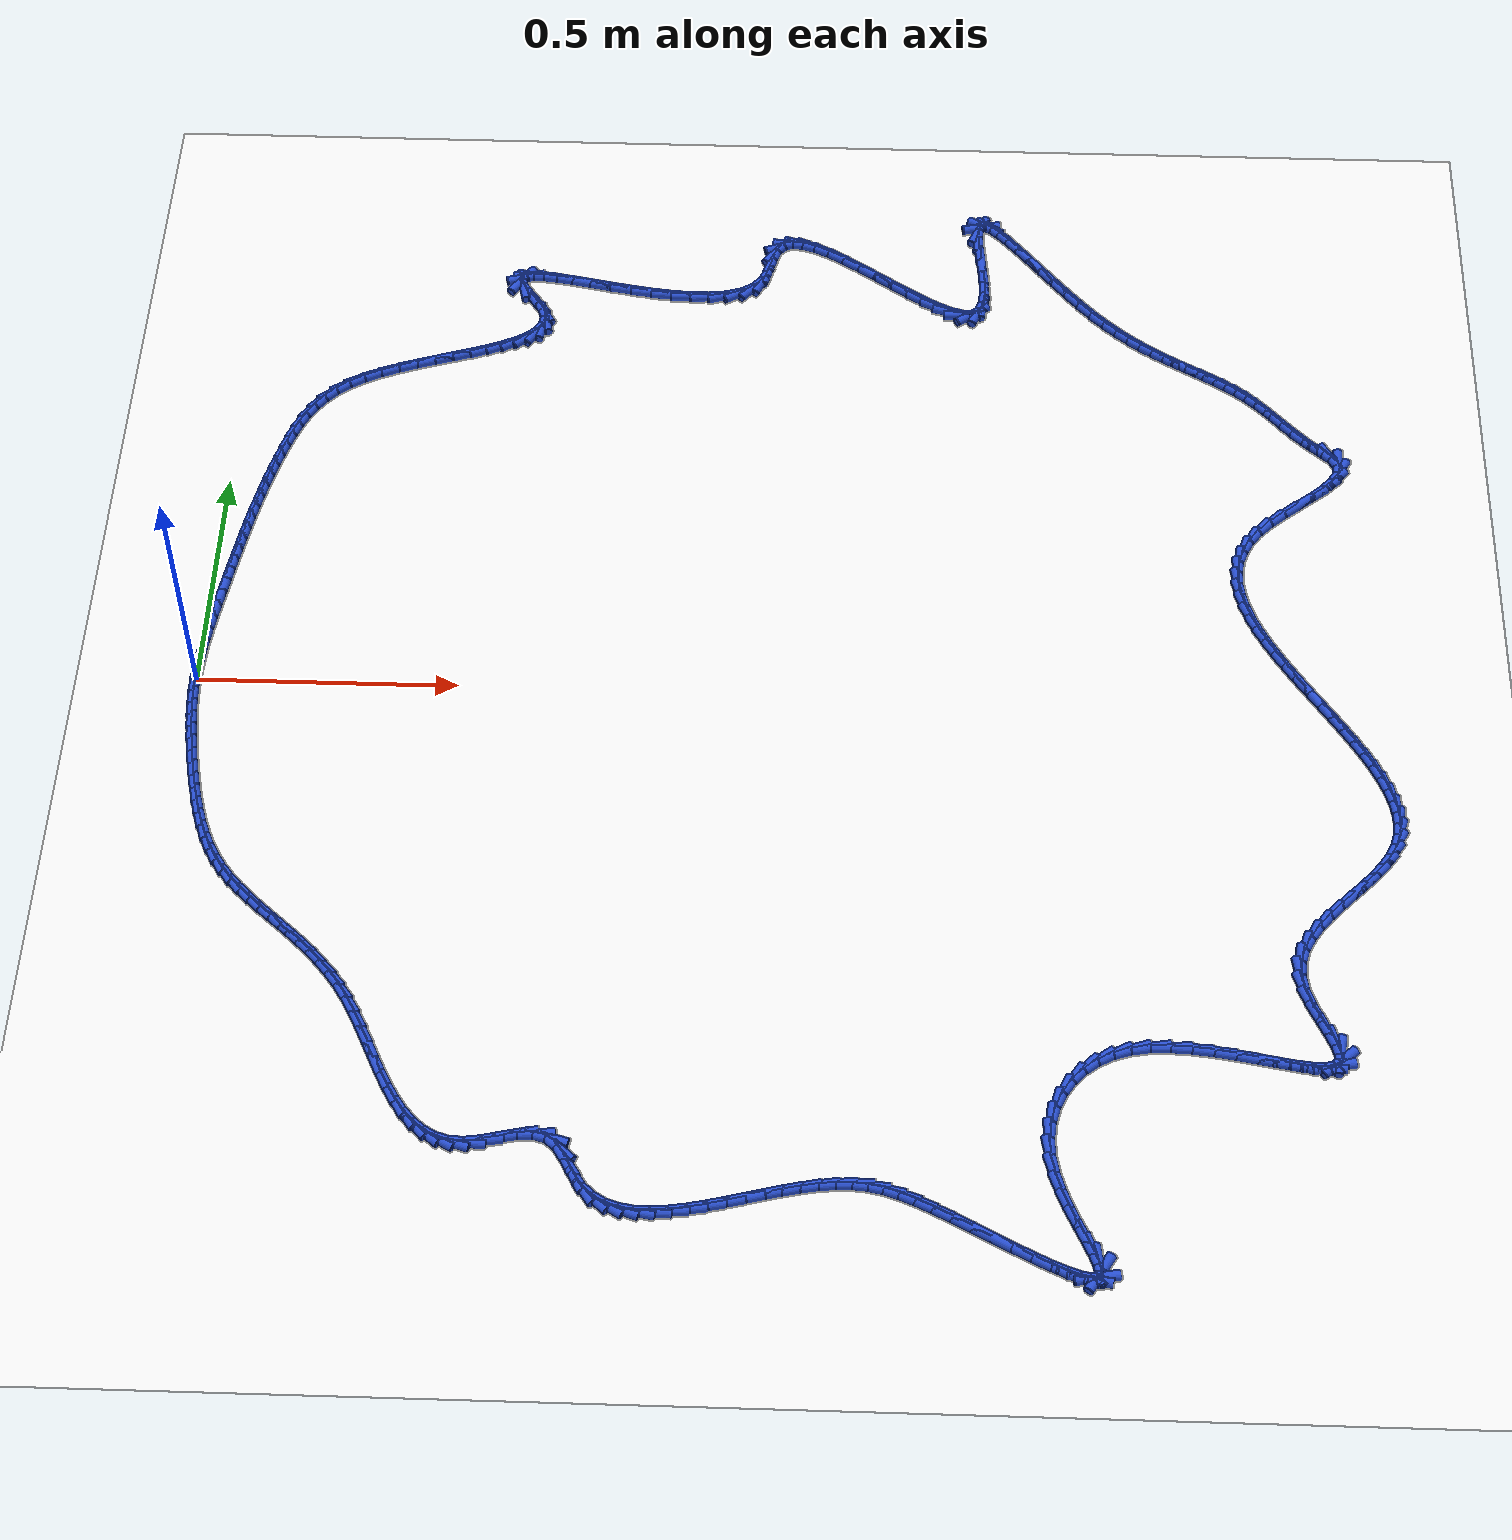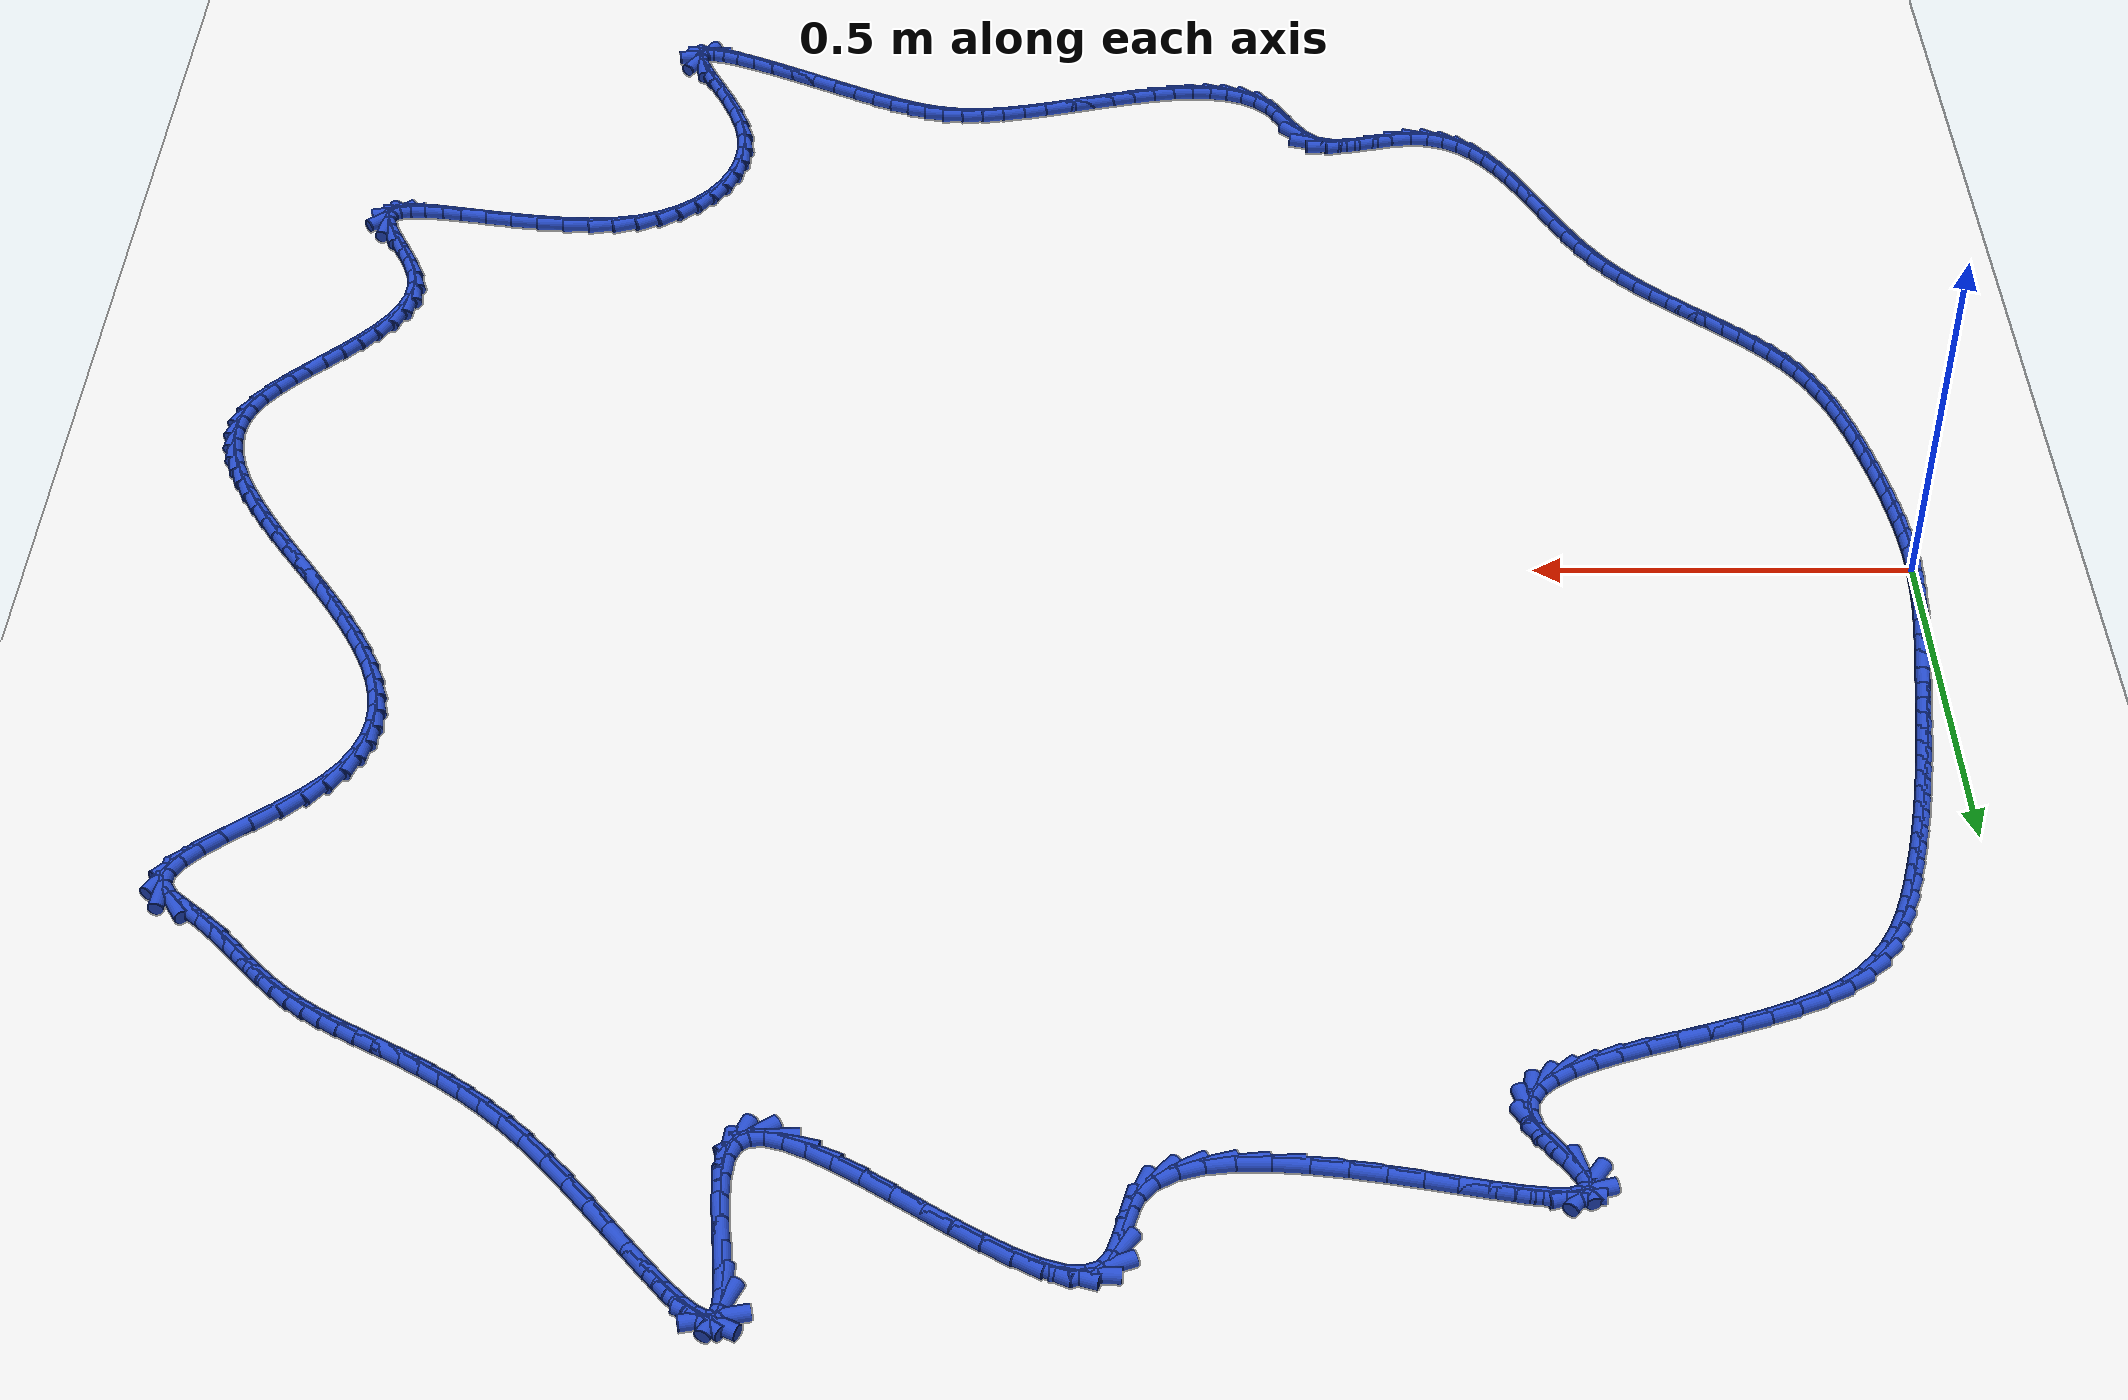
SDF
<sdf version="1.6">
 <world name="default">
  <light name="sun" type="directional">
   <pose>0 0 10 0 -0 0</pose>
   <diffuse>0.8 0.8 0.8 1</diffuse>
   <specular>0.2 0.2 0.2 1</specular>
   <attenuation>
    <range>1000</range>
    <constant>0.9</constant>
    <linear>0.01</linear>
    <quadratic>0.001</quadratic>
   </attenuation>
   <direction>-0.5 0.1 -0.9</direction>
  </light>
  <model name="ground_plane">
   <static>1</static>
   <link name="link">
    <collision name="collision">
     <geometry><plane><normal>0 0 1</normal><size>100 100</size></plane></geometry>
     <surface><friction><ode><mu>100</mu><mu2>50</mu2></ode></friction></surface>
    </collision>
    <visual name="visual">
     <cast_shadows>0</cast_shadows>
     <geometry><plane><normal>0 0 1</normal><size>100 100</size></plane></geometry>
     <material>
      <script><uri>file://media/materials/scripts/gazebo.material</uri><name>Gazebo/WhiteGlow</name></script>
     </material>
    </visual>
   </link>
  </model>
  <gravity>0 0 -9.8</gravity>
  <magnetic_field>6e-06 2.3e-05 -4.2e-05</magnetic_field>
  <atmosphere type="adiabatic"/>
  <physics name="default_physics" default="0" type="ode">
   <max_step_size>0.001</max_step_size>
   <real_time_factor>1</real_time_factor>
   <real_time_update_rate>1000</real_time_update_rate>
  </physics>
  <scene><ambient>0.4 0.4 0.4 1</ambient><background>0.7 0.7 0.7 1</background><shadows>1</shadows></scene>
  <spherical_coordinates>
   <surface_model>EARTH_WGS84</surface_model>
   <latitude_deg>0</latitude_deg>
   <longitude_deg>0</longitude_deg>
   <elevation>0</elevation>
   <heading_deg>0</heading_deg>
  </spherical_coordinates>
  <model name="line">
   <link name="link_0">
    <pose>-2.6020852139652106e-18 -1.3877787807814457e-17 0.01 0 1.57 1.5410836594543111</pose>
    <collision name="collision">
     <geometry><cylinder><radius>0.01</radius><length>0.08</length></cylinder></geometry>
    </collision>
    <visual name="visual">
     <material>
      <script><name>Gazebo/Blue</name><uri>file://media/materials/scripts/gazebo.material</uri></script>
     </material>
     <geometry><cylinder><radius>0.01</radius><length>0.08</length></cylinder></geometry>
    </visual>
   </link>
   <link name="link_1">
    <pose>0.0008448784195982768 0.028426588691219702 0.01 0 1.57 1.5070297732293532</pose>
    <collision name="collision">
     <geometry><cylinder><radius>0.01</radius><length>0.08</length></cylinder></geometry>
    </collision>
    <visual name="visual">
     <material>
      <script><name>Gazebo/Blue</name><uri>file://media/materials/scripts/gazebo.material</uri></script>
     </material>
     <geometry><cylinder><radius>0.01</radius><length>0.08</length></cylinder></geometry>
    </visual>
   </link>
   <link name="link_2">
    <pose>0.0026621797684854044 0.056887238127899954 0.01 0 1.57 1.478518253073047</pose>
    <collision name="collision">
     <geometry><cylinder><radius>0.01</radius><length>0.08</length></cylinder></geometry>
    </collision>
    <visual name="visual">
     <material>
      <script><name>Gazebo/Blue</name><uri>file://media/materials/scripts/gazebo.material</uri></script>
     </material>
     <geometry><cylinder><radius>0.01</radius><length>0.08</length></cylinder></geometry>
    </visual>
   </link>
   <link name="link_3">
    <pose>0.005298386868711799 0.08537418085504456 0.01 0 1.57 1.4554868831947467</pose>
    <collision name="collision">
     <geometry><cylinder><radius>0.01</radius><length>0.08</length></cylinder></geometry>
    </collision>
    <visual name="visual">
     <material>
      <script><name>Gazebo/Blue</name><uri>file://media/materials/scripts/gazebo.material</uri></script>
     </material>
     <geometry><cylinder><radius>0.01</radius><length>0.08</length></cylinder></geometry>
    </visual>
   </link>
   <link name="link_4">
    <pose>0.008599982542327878 0.11387964941765724 0.01 0 1.57 1.4378553510148429</pose>
    <collision name="collision">
     <geometry><cylinder><radius>0.01</radius><length>0.08</length></cylinder></geometry>
    </collision>
    <visual name="visual">
     <material>
      <script><name>Gazebo/Blue</name><uri>file://media/materials/scripts/gazebo.material</uri></script>
     </material>
     <geometry><cylinder><radius>0.01</radius><length>0.08</length></cylinder></geometry>
    </visual>
   </link>
   <link name="link_5">
    <pose>0.01241344961138406 0.14239587636074186 0.01 0 1.57 1.4255454582067757</pose>
    <collision name="collision">
     <geometry><cylinder><radius>0.01</radius><length>0.08</length></cylinder></geometry>
    </collision>
    <visual name="visual">
     <material>
      <script><name>Gazebo/Blue</name><uri>file://media/materials/scripts/gazebo.material</uri></script>
     </material>
     <geometry><cylinder><radius>0.01</radius><length>0.08</length></cylinder></geometry>
    </visual>
   </link>
   <link name="link_6">
    <pose>0.01658527089793076 0.17091509422930218 0.01 0 1.57 1.4184957335514032</pose>
    <collision name="collision">
     <geometry><cylinder><radius>0.01</radius><length>0.08</length></cylinder></geometry>
    </collision>
    <visual name="visual">
     <material>
      <script><name>Gazebo/Blue</name><uri>file://media/materials/scripts/gazebo.material</uri></script>
     </material>
     <geometry><cylinder><radius>0.01</radius><length>0.08</length></cylinder></geometry>
    </visual>
   </link>
   <link name="link_7">
    <pose>0.020961929224018398 0.19942953556834195 0.01 0 1.57 1.416561746177899</pose>
    <collision name="collision">
     <geometry><cylinder><radius>0.01</radius><length>0.08</length></cylinder></geometry>
    </collision>
    <visual name="visual">
     <material>
      <script><name>Gazebo/Blue</name><uri>file://media/materials/scripts/gazebo.material</uri></script>
     </material>
     <geometry><cylinder><radius>0.01</radius><length>0.08</length></cylinder></geometry>
    </visual>
   </link>
   <link name="link_8">
    <pose>0.025393094095717324 0.2279313953311967 0.01 0 1.57 1.4165939329463293</pose>
    <collision name="collision">
     <geometry><cylinder><radius>0.01</radius><length>0.08</length></cylinder></geometry>
    </collision>
    <visual name="visual">
     <material>
      <script><name>Gazebo/Blue</name><uri>file://media/materials/scripts/gazebo.material</uri></script>
     </material>
     <geometry><cylinder><radius>0.01</radius><length>0.08</length></cylinder></geometry>
    </visual>
   </link>
   <link name="link_9">
    <pose>0.029819982731004866 0.25641178853004715 0.01 0 1.57 1.415054781798703</pose>
    <collision name="collision">
     <geometry><cylinder><radius>0.01</radius><length>0.08</length></cylinder></geometry>
    </collision>
    <visual name="visual">
     <material>
      <script><name>Gazebo/Blue</name><uri>file://media/materials/scripts/gazebo.material</uri></script>
     </material>
     <geometry><cylinder><radius>0.01</radius><length>0.08</length></cylinder></geometry>
    </visual>
   </link>
   <link name="link_10">
    <pose>0.034286820481480816 0.28486061504323323 0.01 0 1.57 1.4117509719548476</pose>
    <collision name="collision">
     <geometry><cylinder><radius>0.01</radius><length>0.08</length></cylinder></geometry>
    </collision>
    <visual name="visual">
     <material>
      <script><name>Gazebo/Blue</name><uri>file://media/materials/scripts/gazebo.material</uri></script>
     </material>
     <geometry><cylinder><radius>0.01</radius><length>0.08</length></cylinder></geometry>
    </visual>
   </link>
   <link name="link_11">
    <pose>0.0388433214675514 0.31326771000091974 0.01 0 1.57 1.4066768287680638</pose>
    <collision name="collision">
     <geometry><cylinder><radius>0.01</radius><length>0.08</length></cylinder></geometry>
    </collision>
    <visual name="visual">
     <material>
      <script><name>Gazebo/Blue</name><uri>file://media/materials/scripts/gazebo.material</uri></script>
     </material>
     <geometry><cylinder><radius>0.01</radius><length>0.08</length></cylinder></geometry>
    </visual>
   </link>
   <link name="link_12">
    <pose>0.04353919980962284 0.3416229085332708 0.01 0 1.57 1.3998262561881691</pose>
    <collision name="collision">
     <geometry><cylinder><radius>0.01</radius><length>0.08</length></cylinder></geometry>
    </collision>
    <visual name="visual">
     <material>
      <script><name>Gazebo/Blue</name><uri>file://media/materials/scripts/gazebo.material</uri></script>
     </material>
     <geometry><cylinder><radius>0.01</radius><length>0.08</length></cylinder></geometry>
    </visual>
   </link>
   <link name="link_13">
    <pose>0.04842416962810139 0.3699160457704513 0.01 0 1.57 1.3911932111306324</pose>
    <collision name="collision">
     <geometry><cylinder><radius>0.01</radius><length>0.08</length></cylinder></geometry>
    </collision>
    <visual name="visual">
     <material>
      <script><name>Gazebo/Blue</name><uri>file://media/materials/scripts/gazebo.material</uri></script>
     </material>
     <geometry><cylinder><radius>0.01</radius><length>0.08</length></cylinder></geometry>
    </visual>
   </link>
   <link name="link_14">
    <pose>0.05354794504339329 0.39813695684262534 0.01 0 1.57 1.3807723533890224</pose>
    <collision name="collision">
     <geometry><cylinder><radius>0.01</radius><length>0.08</length></cylinder></geometry>
    </collision>
    <visual name="visual">
     <material>
      <script><name>Gazebo/Blue</name><uri>file://media/materials/scripts/gazebo.material</uri></script>
     </material>
     <geometry><cylinder><radius>0.01</radius><length>0.08</length></cylinder></geometry>
    </visual>
   </link>
   <link name="link_15">
    <pose>0.05896024017590473 0.42627547687995776 0.01 0 1.57 1.36855987432062</pose>
    <collision name="collision">
     <geometry><cylinder><radius>0.01</radius><length>0.08</length></cylinder></geometry>
    </collision>
    <visual name="visual">
     <material>
      <script><name>Gazebo/Blue</name><uri>file://media/materials/scripts/gazebo.material</uri></script>
     </material>
     <geometry><cylinder><radius>0.01</radius><length>0.08</length></cylinder></geometry>
    </visual>
   </link>
   <link name="link_16">
    <pose>0.064710769146042 0.45432144101261285 0.01 0 1.57 1.3545545047957068</pose>
    <collision name="collision">
     <geometry><cylinder><radius>0.01</radius><length>0.08</length></cylinder></geometry>
    </collision>
    <visual name="visual">
     <material>
      <script><name>Gazebo/Blue</name><uri>file://media/materials/scripts/gazebo.material</uri></script>
     </material>
     <geometry><cylinder><radius>0.01</radius><length>0.08</length></cylinder></geometry>
    </visual>
   </link>
   <link name="link_17">
    <pose>0.07084924607421131 0.4822646843707552 0.01 0 1.57 1.338758698098818</pose>
    <collision name="collision">
     <geometry><cylinder><radius>0.01</radius><length>0.08</length></cylinder></geometry>
    </collision>
    <visual name="visual">
     <material>
      <script><name>Gazebo/Blue</name><uri>file://media/materials/scripts/gazebo.material</uri></script>
     </material>
     <geometry><cylinder><radius>0.01</radius><length>0.08</length></cylinder></geometry>
    </visual>
   </link>
   <link name="link_18">
    <pose>0.07742538508081884 0.510095042084549 0.01 0 1.57 1.321179976192636</pose>
    <collision name="collision">
     <geometry><cylinder><radius>0.01</radius><length>0.08</length></cylinder></geometry>
    </collision>
    <visual name="visual">
     <material>
      <script><name>Gazebo/Blue</name><uri>file://media/materials/scripts/gazebo.material</uri></script>
     </material>
     <geometry><cylinder><radius>0.01</radius><length>0.08</length></cylinder></geometry>
    </visual>
   </link>
   <link name="link_19">
    <pose>0.0844889002862709 0.5378023492841593 0.01 0 1.57 1.301832417706088</pose>
    <collision name="collision">
     <geometry><cylinder><radius>0.01</radius><length>0.08</length></cylinder></geometry>
    </collision>
    <visual name="visual">
     <material>
      <script><name>Gazebo/Blue</name><uri>file://media/materials/scripts/gazebo.material</uri></script>
     </material>
     <geometry><cylinder><radius>0.01</radius><length>0.08</length></cylinder></geometry>
    </visual>
   </link>
   <link name="link_20">
    <pose>0.09208950581097375 0.5653764410997506 0.01 0 1.57 1.2807316998429104</pose>
    <collision name="collision">
     <geometry><cylinder><radius>0.01</radius><length>0.08</length></cylinder></geometry>
    </collision>
    <visual name="visual">
     <material>
      <script><name>Gazebo/Blue</name><uri>file://media/materials/scripts/gazebo.material</uri></script>
     </material>
     <geometry><cylinder><radius>0.01</radius><length>0.08</length></cylinder></geometry>
    </visual>
   </link>
   <link name="link_21">
    <pose>0.10027708227318881 0.5928070545724404 0.01 0 1.57 1.2532982697472423</pose>
    <collision name="collision">
     <geometry><cylinder><radius>0.01</radius><length>0.08</length></cylinder></geometry>
    </collision>
    <visual name="visual">
     <material>
      <script><name>Gazebo/Blue</name><uri>file://media/materials/scripts/gazebo.material</uri></script>
     </material>
     <geometry><cylinder><radius>0.01</radius><length>0.08</length></cylinder></geometry>
    </visual>
   </link>
   <link name="link_22">
    <pose>0.10921810005387658 0.6200152401009511 0.01 0 1.57 1.2067108393101946</pose>
    <collision name="collision">
     <geometry><cylinder><radius>0.01</radius><length>0.08</length></cylinder></geometry>
    </collision>
    <visual name="visual">
     <material>
      <script><name>Gazebo/Blue</name><uri>file://media/materials/scripts/gazebo.material</uri></script>
     </material>
     <geometry><cylinder><radius>0.01</radius><length>0.08</length></cylinder></geometry>
    </visual>
   </link>
   <link name="link_23">
    <pose>0.11939962139971863 0.646733177480566 0.01 0 1.57 1.138481220074589</pose>
    <collision name="collision">
     <geometry><cylinder><radius>0.01</radius><length>0.08</length></cylinder></geometry>
    </collision>
    <visual name="visual">
     <material>
      <script><name>Gazebo/Blue</name><uri>file://media/materials/scripts/gazebo.material</uri></script>
     </material>
     <geometry><cylinder><radius>0.01</radius><length>0.08</length></cylinder></geometry>
    </visual>
   </link>
   <link name="link_24">
    <pose>0.13136333243768894 0.672660865885859 0.01 0 1.57 1.0487787142938838</pose>
    <collision name="collision">
     <geometry><cylinder><radius>0.01</radius><length>0.08</length></cylinder></geometry>
    </collision>
    <visual name="visual">
     <material>
      <script><name>Gazebo/Blue</name><uri>file://media/materials/scripts/gazebo.material</uri></script>
     </material>
     <geometry><cylinder><radius>0.01</radius><length>0.08</length></cylinder></geometry>
    </visual>
   </link>
   <link name="link_25">
    <pose>0.14565091929476146 0.6974983044914046 0.01 0 1.57 0.939198202641608</pose>
    <collision name="collision">
     <geometry><cylinder><radius>0.01</radius><length>0.08</length></cylinder></geometry>
    </collision>
    <visual name="visual">
     <material>
      <script><name>Gazebo/Blue</name><uri>file://media/materials/scripts/gazebo.material</uri></script>
     </material>
     <geometry><cylinder><radius>0.01</radius><length>0.08</length></cylinder></geometry>
    </visual>
   </link>
   <link name="link_26">
    <pose>0.16280406809791018 0.7209454924717771 0.01 0 1.57 0.8136660345742998</pose>
    <collision name="collision">
     <geometry><cylinder><radius>0.01</radius><length>0.08</length></cylinder></geometry>
    </collision>
    <visual name="visual">
     <material>
      <script><name>Gazebo/Blue</name><uri>file://media/materials/scripts/gazebo.material</uri></script>
     </material>
     <geometry><cylinder><radius>0.01</radius><length>0.08</length></cylinder></geometry>
    </visual>
   </link>
   <link name="link_27">
    <pose>0.18336446497410896 0.7427024290015501 0.01 0 1.57 0.6787059309352872</pose>
    <collision name="collision">
     <geometry><cylinder><radius>0.01</radius><length>0.08</length></cylinder></geometry>
    </collision>
    <visual name="visual">
     <material>
      <script><name>Gazebo/Blue</name><uri>file://media/materials/scripts/gazebo.material</uri></script>
     </material>
     <geometry><cylinder><radius>0.01</radius><length>0.08</length></cylinder></geometry>
    </visual>
   </link>
   <link name="link_28">
    <pose>0.20787326473798368 0.7624693472510563 0.01 0 1.57 0.5515470152467176</pose>
    <collision name="collision">
     <geometry><cylinder><radius>0.01</radius><length>0.08</length></cylinder></geometry>
    </collision>
    <visual name="visual">
     <material>
      <script><name>Gazebo/Blue</name><uri>file://media/materials/scripts/gazebo.material</uri></script>
     </material>
     <geometry><cylinder><radius>0.01</radius><length>0.08</length></cylinder></geometry>
    </visual>
   </link>
   <link name="link_29">
    <pose>0.23652710004693395 0.7800982117087109 0.01 0 1.57 0.4567981321654271</pose>
    <collision name="collision">
     <geometry><cylinder><radius>0.01</radius><length>0.08</length></cylinder></geometry>
    </collision>
    <visual name="visual">
     <material>
      <script><name>Gazebo/Blue</name><uri>file://media/materials/scripts/gazebo.material</uri></script>
     </material>
     <geometry><cylinder><radius>0.01</radius><length>0.08</length></cylinder></geometry>
    </visual>
   </link>
   <link name="link_30">
    <pose>0.2685853200939517 0.7958537767299718 0.01 0 1.57 0.39021845529984667</pose>
    <collision name="collision">
     <geometry><cylinder><radius>0.01</radius><length>0.08</length></cylinder></geometry>
    </collision>
    <visual name="visual">
     <material>
      <script><name>Gazebo/Blue</name><uri>file://media/materials/scripts/gazebo.material</uri></script>
     </material>
     <geometry><cylinder><radius>0.01</radius><length>0.08</length></cylinder></geometry>
    </visual>
   </link>
   <link name="link_31">
    <pose>0.30314938492295745 0.8100703327747175 0.01 0 1.57 0.34531435196308385</pose>
    <collision name="collision">
     <geometry><cylinder><radius>0.01</radius><length>0.08</length></cylinder></geometry>
    </collision>
    <visual name="visual">
     <material>
      <script><name>Gazebo/Blue</name><uri>file://media/materials/scripts/gazebo.material</uri></script>
     </material>
     <geometry><cylinder><radius>0.01</radius><length>0.08</length></cylinder></geometry>
    </visual>
   </link>
   <link name="link_32">
    <pose>0.3393207545778715 0.8230821703028263 0.01 0 1.57 0.31803743105901944</pose>
    <collision name="collision">
     <geometry><cylinder><radius>0.01</radius><length>0.08</length></cylinder></geometry>
    </collision>
    <visual name="visual">
     <material>
      <script><name>Gazebo/Blue</name><uri>file://media/materials/scripts/gazebo.material</uri></script>
     </material>
     <geometry><cylinder><radius>0.01</radius><length>0.08</length></cylinder></geometry>
    </visual>
   </link>
   <link name="link_33">
    <pose>0.37620088910261407 0.8352235797741762 0.01 0 1.57 0.30634578979641996</pose>
    <collision name="collision">
     <geometry><cylinder><radius>0.01</radius><length>0.08</length></cylinder></geometry>
    </collision>
    <visual name="visual">
     <material>
      <script><name>Gazebo/Blue</name><uri>file://media/materials/scripts/gazebo.material</uri></script>
     </material>
     <geometry><cylinder><radius>0.01</radius><length>0.08</length></cylinder></geometry>
    </visual>
   </link>
   <link name="link_34">
    <pose>0.41289124854110515 0.8468288516486453 0.01 0 1.57 0.30997734498890184</pose>
    <collision name="collision">
     <geometry><cylinder><radius>0.01</radius><length>0.08</length></cylinder></geometry>
    </collision>
    <visual name="visual">
     <material>
      <script><name>Gazebo/Blue</name><uri>file://media/materials/scripts/gazebo.material</uri></script>
     </material>
     <geometry><cylinder><radius>0.01</radius><length>0.08</length></cylinder></geometry>
    </visual>
   </link>
   <link name="link_35">
    <pose>0.4484932929372652 0.858232276386112 0.01 0 1.57 0.3305810963488139</pose>
    <collision name="collision">
     <geometry><cylinder><radius>0.01</radius><length>0.08</length></cylinder></geometry>
    </collision>
    <visual name="visual">
     <material>
      <script><name>Gazebo/Blue</name><uri>file://media/materials/scripts/gazebo.material</uri></script>
     </material>
     <geometry><cylinder><radius>0.01</radius><length>0.08</length></cylinder></geometry>
    </visual>
   </link>
   <link name="link_36">
    <pose>0.48210848233501463 0.8697681444464549 0.01 0 1.57 0.3723638851385659</pose>
    <collision name="collision">
     <geometry><cylinder><radius>0.01</radius><length>0.08</length></cylinder></geometry>
    </collision>
    <visual name="visual">
     <material>
      <script><name>Gazebo/Blue</name><uri>file://media/materials/scripts/gazebo.material</uri></script>
     </material>
     <geometry><cylinder><radius>0.01</radius><length>0.08</length></cylinder></geometry>
    </visual>
   </link>
   <link name="link_37">
    <pose>0.5128382767782735 0.8817707462895515 0.01 0 1.57 0.4435798267506703</pose>
    <collision name="collision">
     <geometry><cylinder><radius>0.01</radius><length>0.08</length></cylinder></geometry>
    </collision>
    <visual name="visual">
     <material>
      <script><name>Gazebo/Blue</name><uri>file://media/materials/scripts/gazebo.material</uri></script>
     </material>
     <geometry><cylinder><radius>0.01</radius><length>0.08</length></cylinder></geometry>
    </visual>
   </link>
   <link name="link_38">
    <pose>0.539784136310962 0.8945743723752806 0.01 0 1.57 0.5593846322800319</pose>
    <collision name="collision">
     <geometry><cylinder><radius>0.01</radius><length>0.08</length></cylinder></geometry>
    </collision>
    <visual name="visual">
     <material>
      <script><name>Gazebo/Blue</name><uri>file://media/materials/scripts/gazebo.material</uri></script>
     </material>
     <geometry><cylinder><radius>0.01</radius><length>0.08</length></cylinder></geometry>
    </visual>
   </link>
   <link name="link_39">
    <pose>0.5620475209770007 0.9085133131635202 0.01 0 1.57 0.7457247708682181</pose>
    <collision name="collision">
     <geometry><cylinder><radius>0.01</radius><length>0.08</length></cylinder></geometry>
    </collision>
    <visual name="visual">
     <material>
      <script><name>Gazebo/Blue</name><uri>file://media/materials/scripts/gazebo.material</uri></script>
     </material>
     <geometry><cylinder><radius>0.01</radius><length>0.08</length></cylinder></geometry>
    </visual>
   </link>
   <link name="link_40">
    <pose>0.5787298908203096 0.9239218591141487 0.01 0 1.57 1.035718730863639</pose>
    <collision name="collision">
     <geometry><cylinder><radius>0.01</radius><length>0.08</length></cylinder></geometry>
    </collision>
    <visual name="visual">
     <material>
      <script><name>Gazebo/Blue</name><uri>file://media/materials/scripts/gazebo.material</uri></script>
     </material>
     <geometry><cylinder><radius>0.01</radius><length>0.08</length></cylinder></geometry>
    </visual>
   </link>
   <link name="link_41">
    <pose>0.5889327058848091 0.9411343006870445 0.01 0 1.57 1.425844484476826</pose>
    <collision name="collision">
     <geometry><cylinder><radius>0.01</radius><length>0.08</length></cylinder></geometry>
    </collision>
    <visual name="visual">
     <material>
      <script><name>Gazebo/Blue</name><uri>file://media/materials/scripts/gazebo.material</uri></script>
     </material>
     <geometry><cylinder><radius>0.01</radius><length>0.08</length></cylinder></geometry>
    </visual>
   </link>
   <link name="link_42">
    <pose>0.5917574262144193 0.9604849283420853 0.01 0 1.57 -1.3259842156426436</pose>
    <collision name="collision">
     <geometry><cylinder><radius>0.01</radius><length>0.08</length></cylinder></geometry>
    </collision>
    <visual name="visual">
     <material>
      <script><name>Gazebo/Blue</name><uri>file://media/materials/scripts/gazebo.material</uri></script>
     </material>
     <geometry><cylinder><radius>0.01</radius><length>0.08</length></cylinder></geometry>
    </visual>
   </link>
   <link name="link_43">
    <pose>0.5863055118530607 0.9823080325391496 0.01 0 1.57 -1.0459115863139774</pose>
    <collision name="collision">
     <geometry><cylinder><radius>0.01</radius><length>0.08</length></cylinder></geometry>
    </collision>
    <visual name="visual">
     <material>
      <script><name>Gazebo/Blue</name><uri>file://media/materials/scripts/gazebo.material</uri></script>
     </material>
     <geometry><cylinder><radius>0.01</radius><length>0.08</length></cylinder></geometry>
    </visual>
   </link>
   <link name="link_44">
    <pose>0.5721767744905015 1.006707208733822 0.01 0 1.57 -0.9435112723755731</pose>
    <collision name="collision">
     <geometry><cylinder><radius>0.01</radius><length>0.08</length></cylinder></geometry>
    </collision>
    <visual name="visual">
     <material>
      <script><name>Gazebo/Blue</name><uri>file://media/materials/scripts/gazebo.material</uri></script>
     </material>
     <geometry><cylinder><radius>0.01</radius><length>0.08</length></cylinder></geometry>
    </visual>
   </link>
   <link name="link_45">
    <pose>0.5543511150022675 1.0312955224353124 0.01 0 1.57 -1.0042993922145915</pose>
    <collision name="collision">
     <geometry><cylinder><radius>0.01</radius><length>0.08</length></cylinder></geometry>
    </collision>
    <visual name="visual">
     <material>
      <script><name>Gazebo/Blue</name><uri>file://media/materials/scripts/gazebo.material</uri></script>
     </material>
     <geometry><cylinder><radius>0.01</radius><length>0.08</length></cylinder></geometry>
    </visual>
   </link>
   <link name="link_46">
    <pose>0.5410694321673851 1.05217744566448 0.01 0 1.57 -1.344952709872613</pose>
    <collision name="collision">
     <geometry><cylinder><radius>0.01</radius><length>0.08</length></cylinder></geometry>
    </collision>
    <visual name="visual">
     <material>
      <script><name>Gazebo/Blue</name><uri>file://media/materials/scripts/gazebo.material</uri></script>
     </material>
     <geometry><cylinder><radius>0.01</radius><length>0.08</length></cylinder></geometry>
    </visual>
   </link>
   <link name="link_47">
    <pose>0.5376826420435615 1.066917786595661 0.01 0 1.57 0.9791760040284256</pose>
    <collision name="collision">
     <geometry><cylinder><radius>0.01</radius><length>0.08</length></cylinder></geometry>
    </collision>
    <visual name="visual">
     <material>
      <script><name>Gazebo/Blue</name><uri>file://media/materials/scripts/gazebo.material</uri></script>
     </material>
     <geometry><cylinder><radius>0.01</radius><length>0.08</length></cylinder></geometry>
    </visual>
   </link>
   <link name="link_48">
    <pose>0.5437781699800907 1.0759897963050913 0.01 0 1.57 0.2830122267667571</pose>
    <collision name="collision">
     <geometry><cylinder><radius>0.01</radius><length>0.08</length></cylinder></geometry>
    </collision>
    <visual name="visual">
     <material>
      <script><name>Gazebo/Blue</name><uri>file://media/materials/scripts/gazebo.material</uri></script>
     </material>
     <geometry><cylinder><radius>0.01</radius><length>0.08</length></cylinder></geometry>
    </visual>
   </link>
   <link name="link_49">
    <pose>0.5582728637803533 1.0802051208803385 0.01 0 1.57 0.007807269390180042</pose>
    <collision name="collision">
     <geometry><cylinder><radius>0.01</radius><length>0.08</length></cylinder></geometry>
    </collision>
    <visual name="visual">
     <material>
      <script><name>Gazebo/Blue</name><uri>file://media/materials/scripts/gazebo.material</uri></script>
     </material>
     <geometry><cylinder><radius>0.01</radius><length>0.08</length></cylinder></geometry>
    </visual>
   </link>
   <link name="link_50">
    <pose>0.5800835712477308 1.0803754064089712 0.01 0 1.57 -0.10879544085884654</pose>
    <collision name="collision">
     <geometry><cylinder><radius>0.01</radius><length>0.08</length></cylinder></geometry>
    </collision>
    <visual name="visual">
     <material>
      <script><name>Gazebo/Blue</name><uri>file://media/materials/scripts/gazebo.material</uri></script>
     </material>
     <geometry><cylinder><radius>0.01</radius><length>0.08</length></cylinder></geometry>
    </visual>
   </link>
   <link name="link_51">
    <pose>0.6081271401856042 1.0773122989785566 0.01 0 1.57 -0.16376016130478466</pose>
    <collision name="collision">
     <geometry><cylinder><radius>0.01</radius><length>0.08</length></cylinder></geometry>
    </collision>
    <visual name="visual">
     <material>
      <script><name>Gazebo/Blue</name><uri>file://media/materials/scripts/gazebo.material</uri></script>
     </material>
     <geometry><cylinder><radius>0.01</radius><length>0.08</length></cylinder></geometry>
    </visual>
   </link>
   <link name="link_52">
    <pose>0.6413204183973549 1.0718274446766622 0.01 0 1.57 -0.18816565636135835</pose>
    <collision name="collision">
     <geometry><cylinder><radius>0.01</radius><length>0.08</length></cylinder></geometry>
    </collision>
    <visual name="visual">
     <material>
      <script><name>Gazebo/Blue</name><uri>file://media/materials/scripts/gazebo.material</uri></script>
     </material>
     <geometry><cylinder><radius>0.01</radius><length>0.08</length></cylinder></geometry>
    </visual>
   </link>
   <link name="link_53">
    <pose>0.6785802536863641 1.0647324895908563 0.01 0 1.57 -0.19368368983215872</pose>
    <collision name="collision">
     <geometry><cylinder><radius>0.01</radius><length>0.08</length></cylinder></geometry>
    </collision>
    <visual name="visual">
     <material>
      <script><name>Gazebo/Blue</name><uri>file://media/materials/scripts/gazebo.material</uri></script>
     </material>
     <geometry><cylinder><radius>0.01</radius><length>0.08</length></cylinder></geometry>
    </visual>
   </link>
   <link name="link_54">
    <pose>0.7188234938560124 1.056839079808707 0.01 0 1.57 -0.18485079265071616</pose>
    <collision name="collision">
     <geometry><cylinder><radius>0.01</radius><length>0.08</length></cylinder></geometry>
    </collision>
    <visual name="visual">
     <material>
      <script><name>Gazebo/Blue</name><uri>file://media/materials/scripts/gazebo.material</uri></script>
     </material>
     <geometry><cylinder><radius>0.01</radius><length>0.08</length></cylinder></geometry>
    </visual>
   </link>
   <link name="link_55">
    <pose>0.760966986709682 1.048958861417781 0.01 0 1.57 -0.1627760877235763</pose>
    <collision name="collision">
     <geometry><cylinder><radius>0.01</radius><length>0.08</length></cylinder></geometry>
    </collision>
    <visual name="visual">
     <material>
      <script><name>Gazebo/Blue</name><uri>file://media/materials/scripts/gazebo.material</uri></script>
     </material>
     <geometry><cylinder><radius>0.01</radius><length>0.08</length></cylinder></geometry>
    </visual>
   </link>
   <link name="link_56">
    <pose>0.8039275800507533 1.0419034805056469 0.01 0 1.57 -0.12624745341101354</pose>
    <collision name="collision">
     <geometry><cylinder><radius>0.01</radius><length>0.08</length></cylinder></geometry>
    </collision>
    <visual name="visual">
     <material>
      <script><name>Gazebo/Blue</name><uri>file://media/materials/scripts/gazebo.material</uri></script>
     </material>
     <geometry><cylinder><radius>0.01</radius><length>0.08</length></cylinder></geometry>
    </visual>
   </link>
   <link name="link_57">
    <pose>0.846622121682608 1.0364845831598724 0.01 0 1.57 -0.07172927232584644</pose>
    <collision name="collision">
     <geometry><cylinder><radius>0.01</radius><length>0.08</length></cylinder></geometry>
    </collision>
    <visual name="visual">
     <material>
      <script><name>Gazebo/Blue</name><uri>file://media/materials/scripts/gazebo.material</uri></script>
     </material>
     <geometry><cylinder><radius>0.01</radius><length>0.08</length></cylinder></geometry>
    </visual>
   </link>
   <link name="link_58">
    <pose>0.8879674594086271 1.033513815468025 0.01 0 1.57 0.007426897754686918</pose>
    <collision name="collision">
     <geometry><cylinder><radius>0.01</radius><length>0.08</length></cylinder></geometry>
    </collision>
    <visual name="visual">
     <material>
      <script><name>Gazebo/Blue</name><uri>file://media/materials/scripts/gazebo.material</uri></script>
     </material>
     <geometry><cylinder><radius>0.01</radius><length>0.08</length></cylinder></geometry>
    </visual>
   </link>
   <link name="link_59">
    <pose>0.9268804410321914 1.0338028235176728 0.01 0 1.57 0.12256730114680607</pose>
    <collision name="collision">
     <geometry><cylinder><radius>0.01</radius><length>0.08</length></cylinder></geometry>
    </collision>
    <visual name="visual">
     <material>
      <script><name>Gazebo/Blue</name><uri>file://media/materials/scripts/gazebo.material</uri></script>
     </material>
     <geometry><cylinder><radius>0.01</radius><length>0.08</length></cylinder></geometry>
    </visual>
   </link>
   <link name="link_60">
    <pose>0.9622779143566829 1.0381632533963836 0.01 0 1.57 0.29157159140706174</pose>
    <collision name="collision">
     <geometry><cylinder><radius>0.01</radius><length>0.08</length></cylinder></geometry>
    </collision>
    <visual name="visual">
     <material>
      <script><name>Gazebo/Blue</name><uri>file://media/materials/scripts/gazebo.material</uri></script>
     </material>
     <geometry><cylinder><radius>0.01</radius><length>0.08</length></cylinder></geometry>
    </visual>
   </link>
   <link name="link_61">
    <pose>0.993076727185482 1.0474067511917244 0.01 0 1.57 0.5365466157539174</pose>
    <collision name="collision">
     <geometry><cylinder><radius>0.01</radius><length>0.08</length></cylinder></geometry>
    </collision>
    <visual name="visual">
     <material>
      <script><name>Gazebo/Blue</name><uri>file://media/materials/scripts/gazebo.material</uri></script>
     </material>
     <geometry><cylinder><radius>0.01</radius><length>0.08</length></cylinder></geometry>
    </visual>
   </link>
   <link name="link_62">
    <pose>1.0181937273219703 1.0623449629912642 0.01 0 1.57 0.8629508604575247</pose>
    <collision name="collision">
     <geometry><cylinder><radius>0.01</radius><length>0.08</length></cylinder></geometry>
    </collision>
    <visual name="visual">
     <material>
      <script><name>Gazebo/Blue</name><uri>file://media/materials/scripts/gazebo.material</uri></script>
     </material>
     <geometry><cylinder><radius>0.01</radius><length>0.08</length></cylinder></geometry>
    </visual>
   </link>
   <link name="link_63">
    <pose>1.0365457625695291 1.0837895348825701 0.01 0 1.57 1.182268750996283</pose>
    <collision name="collision">
     <geometry><cylinder><radius>0.01</radius><length>0.08</length></cylinder></geometry>
    </collision>
    <visual name="visual">
     <material>
      <script><name>Gazebo/Blue</name><uri>file://media/materials/scripts/gazebo.material</uri></script>
     </material>
     <geometry><cylinder><radius>0.01</radius><length>0.08</length></cylinder></geometry>
    </visual>
   </link>
   <link name="link_64">
    <pose>1.047901483114695 1.11153142778282 0.01 0 1.57 1.318170365950178</pose>
    <collision name="collision">
     <geometry><cylinder><radius>0.01</radius><length>0.08</length></cylinder></geometry>
    </collision>
    <visual name="visual">
     <material>
      <script><name>Gazebo/Blue</name><uri>file://media/materials/scripts/gazebo.material</uri></script>
     </material>
     <geometry><cylinder><radius>0.01</radius><length>0.08</length></cylinder></geometry>
    </visual>
   </link>
   <link name="link_65">
    <pose>1.0555465507052335 1.1411472899756216 0.01 0 1.57 1.2675876353500377</pose>
    <collision name="collision">
     <geometry><cylinder><radius>0.01</radius><length>0.08</length></cylinder></geometry>
    </collision>
    <visual name="visual">
     <material>
      <script><name>Gazebo/Blue</name><uri>file://media/materials/scripts/gazebo.material</uri></script>
     </material>
     <geometry><cylinder><radius>0.01</radius><length>0.08</length></cylinder></geometry>
    </visual>
   </link>
   <link name="link_66">
    <pose>1.0636742093600924 1.1671262454743698 0.01 0 1.57 0.9421194328646237</pose>
    <collision name="collision">
     <geometry><cylinder><radius>0.01</radius><length>0.08</length></cylinder></geometry>
    </collision>
    <visual name="visual">
     <material>
      <script><name>Gazebo/Blue</name><uri>file://media/materials/scripts/gazebo.material</uri></script>
     </material>
     <geometry><cylinder><radius>0.01</radius><length>0.08</length></cylinder></geometry>
    </visual>
   </link>
   <link name="link_67">
    <pose>1.076195614323961 1.184347499382781 0.01 0 1.57 0.39113382868434315</pose>
    <collision name="collision">
     <geometry><cylinder><radius>0.01</radius><length>0.08</length></cylinder></geometry>
    </collision>
    <visual name="visual">
     <material>
      <script><name>Gazebo/Blue</name><uri>file://media/materials/scripts/gazebo.material</uri></script>
     </material>
     <geometry><cylinder><radius>0.01</radius><length>0.08</length></cylinder></geometry>
    </visual>
   </link>
   <link name="link_68">
    <pose>1.09409991679033 1.1917308924832453 0.01 0 1.57 -0.050722573367266585</pose>
    <collision name="collision">
     <geometry><cylinder><radius>0.01</radius><length>0.08</length></cylinder></geometry>
    </collision>
    <visual name="visual">
     <material>
      <script><name>Gazebo/Blue</name><uri>file://media/materials/scripts/gazebo.material</uri></script>
     </material>
     <geometry><cylinder><radius>0.01</radius><length>0.08</length></cylinder></geometry>
    </visual>
   </link>
   <link name="link_69">
    <pose>1.1166479646959675 1.1905862156336227 0.01 0 1.57 -0.30537885236668416</pose>
    <collision name="collision">
     <geometry><cylinder><radius>0.01</radius><length>0.08</length></cylinder></geometry>
    </collision>
    <visual name="visual">
     <material>
      <script><name>Gazebo/Blue</name><uri>file://media/materials/scripts/gazebo.material</uri></script>
     </material>
     <geometry><cylinder><radius>0.01</radius><length>0.08</length></cylinder></geometry>
    </visual>
   </link>
   <link name="link_70">
    <pose>1.1430780937698428 1.182254390254374 0.01 0 1.57 -0.44734917595654355</pose>
    <collision name="collision">
     <geometry><cylinder><radius>0.01</radius><length>0.08</length></cylinder></geometry>
    </collision>
    <visual name="visual">
     <material>
      <script><name>Gazebo/Blue</name><uri>file://media/materials/scripts/gazebo.material</uri></script>
     </material>
     <geometry><cylinder><radius>0.01</radius><length>0.08</length></cylinder></geometry>
    </visual>
   </link>
   <link name="link_71">
    <pose>1.1726286397409256 1.1680763377659598 0.01 0 1.57 -0.5297003296626155</pose>
    <collision name="collision">
     <geometry><cylinder><radius>0.01</radius><length>0.08</length></cylinder></geometry>
    </collision>
    <visual name="visual">
     <material>
      <script><name>Gazebo/Blue</name><uri>file://media/materials/scripts/gazebo.material</uri></script>
     </material>
     <geometry><cylinder><radius>0.01</radius><length>0.08</length></cylinder></geometry>
    </visual>
   </link>
   <link name="link_72">
    <pose>1.2045379383381851 1.1493929795888413 0.01 0 1.57 -0.5778129608776233</pose>
    <collision name="collision">
     <geometry><cylinder><radius>0.01</radius><length>0.08</length></cylinder></geometry>
    </collision>
    <visual name="visual">
     <material>
      <script><name>Gazebo/Blue</name><uri>file://media/materials/scripts/gazebo.material</uri></script>
     </material>
     <geometry><cylinder><radius>0.01</radius><length>0.08</length></cylinder></geometry>
    </visual>
   </link>
   <link name="link_73">
    <pose>1.2380443252905904 1.127545237143479 0.01 0 1.57 -0.6034966566351577</pose>
    <collision name="collision">
     <geometry><cylinder><radius>0.01</radius><length>0.08</length></cylinder></geometry>
    </collision>
    <visual name="visual">
     <material>
      <script><name>Gazebo/Blue</name><uri>file://media/materials/scripts/gazebo.material</uri></script>
     </material>
     <geometry><cylinder><radius>0.01</radius><length>0.08</length></cylinder></geometry>
    </visual>
   </link>
   <link name="link_74">
    <pose>1.2723861363271114 1.1038740318503348 0.01 0 1.57 -0.6119505003149199</pose>
    <collision name="collision">
     <geometry><cylinder><radius>0.01</radius><length>0.08</length></cylinder></geometry>
    </collision>
    <visual name="visual">
     <material>
      <script><name>Gazebo/Blue</name><uri>file://media/materials/scripts/gazebo.material</uri></script>
     </material>
     <geometry><cylinder><radius>0.01</radius><length>0.08</length></cylinder></geometry>
    </visual>
   </link>
   <link name="link_75">
    <pose>1.3068017071767173 1.0797202851298688 0.01 0 1.57 -0.6044503724012126</pose>
    <collision name="collision">
     <geometry><cylinder><radius>0.01</radius><length>0.08</length></cylinder></geometry>
    </collision>
    <visual name="visual">
     <material>
      <script><name>Gazebo/Blue</name><uri>file://media/materials/scripts/gazebo.material</uri></script>
     </material>
     <geometry><cylinder><radius>0.01</radius><length>0.08</length></cylinder></geometry>
    </visual>
   </link>
   <link name="link_76">
    <pose>1.340529373568377 1.056424918402543 0.01 0 1.57 -0.578882292504587</pose>
    <collision name="collision">
     <geometry><cylinder><radius>0.01</radius><length>0.08</length></cylinder></geometry>
    </collision>
    <visual name="visual">
     <material>
      <script><name>Gazebo/Blue</name><uri>file://media/materials/scripts/gazebo.material</uri></script>
     </material>
     <geometry><cylinder><radius>0.01</radius><length>0.08</length></cylinder></geometry>
    </visual>
   </link>
   <link name="link_77">
    <pose>1.3728074712310607 1.0353288530888167 0.01 0 1.57 -0.5284921865191576</pose>
    <collision name="collision">
     <geometry><cylinder><radius>0.01</radius><length>0.08</length></cylinder></geometry>
    </collision>
    <visual name="visual">
     <material>
      <script><name>Gazebo/Blue</name><uri>file://media/materials/scripts/gazebo.material</uri></script>
     </material>
     <geometry><cylinder><radius>0.01</radius><length>0.08</length></cylinder></geometry>
    </visual>
   </link>
   <link name="link_78">
    <pose>1.402874335893737 1.0177730106091518 0.01 0 1.57 -0.43756166036817484</pose>
    <collision name="collision">
     <geometry><cylinder><radius>0.01</radius><length>0.08</length></cylinder></geometry>
    </collision>
    <visual name="visual">
     <material>
      <script><name>Gazebo/Blue</name><uri>file://media/materials/scripts/gazebo.material</uri></script>
     </material>
     <geometry><cylinder><radius>0.01</radius><length>0.08</length></cylinder></geometry>
    </visual>
   </link>
   <link name="link_79">
    <pose>1.4299683032853765 1.0050983123840094 0.01 0 1.57 -0.26951191261038004</pose>
    <collision name="collision">
     <geometry><cylinder><radius>0.01</radius><length>0.08</length></cylinder></geometry>
    </collision>
    <visual name="visual">
     <material>
      <script><name>Gazebo/Blue</name><uri>file://media/materials/scripts/gazebo.material</uri></script>
     </material>
     <geometry><cylinder><radius>0.01</radius><length>0.08</length></cylinder></geometry>
    </visual>
   </link>
   <link name="link_80">
    <pose>1.453327709134947 0.9986456798338501 0.01 0 1.57 0.058795747686479695</pose>
    <collision name="collision">
     <geometry><cylinder><radius>0.01</radius><length>0.08</length></cylinder></geometry>
    </collision>
    <visual name="visual">
     <material>
      <script><name>Gazebo/Blue</name><uri>file://media/materials/scripts/gazebo.material</uri></script>
     </material>
     <geometry><cylinder><radius>0.01</radius><length>0.08</length></cylinder></geometry>
    </visual>
   </link>
   <link name="link_81">
    <pose>1.472190889171419 0.9997560343791351 0.01 0 1.57 0.6345174181482096</pose>
    <collision name="collision">
     <geometry><cylinder><radius>0.01</radius><length>0.08</length></cylinder></geometry>
    </collision>
    <visual name="visual">
     <material>
      <script><name>Gazebo/Blue</name><uri>file://media/materials/scripts/gazebo.material</uri></script>
     </material>
     <geometry><cylinder><radius>0.01</radius><length>0.08</length></cylinder></geometry>
    </visual>
   </link>
   <link name="link_82">
    <pose>1.4857961791979561 1.0097702972987173 0.01 0 1.57 1.186503560602105</pose>
    <collision name="collision">
     <geometry><cylinder><radius>0.01</radius><length>0.08</length></cylinder></geometry>
    </collision>
    <visual name="visual">
     <material>
      <script><name>Gazebo/Blue</name><uri>file://media/materials/scripts/gazebo.material</uri></script>
     </material>
     <geometry><cylinder><radius>0.01</radius><length>0.08</length></cylinder></geometry>
    </visual>
   </link>
   <link name="link_83">
    <pose>1.4937245086214528 1.0293755176069175 0.01 0 1.57 1.4549673758504158</pose>
    <collision name="collision">
     <geometry><cylinder><radius>0.01</radius><length>0.08</length></cylinder></geometry>
    </collision>
    <visual name="visual">
     <material>
      <script><name>Gazebo/Blue</name><uri>file://media/materials/scripts/gazebo.material</uri></script>
     </material>
     <geometry><cylinder><radius>0.01</radius><length>0.08</length></cylinder></geometry>
    </visual>
   </link>
   <link name="link_84">
    <pose>1.4969025685845991 1.0566902308836934 0.01 0 1.57 -1.5611042230392178</pose>
    <collision name="collision">
     <geometry><cylinder><radius>0.01</radius><length>0.08</length></cylinder></geometry>
    </collision>
    <visual name="visual">
     <material>
      <script><name>Gazebo/Blue</name><uri>file://media/materials/scripts/gazebo.material</uri></script>
     </material>
     <geometry><cylinder><radius>0.01</radius><length>0.08</length></cylinder></geometry>
    </visual>
   </link>
   <link name="link_85">
    <pose>1.4965874476133965 1.0892023780835693 0.01 0 1.57 -1.498440108289049</pose>
    <collision name="collision">
     <geometry><cylinder><radius>0.01</radius><length>0.08</length></cylinder></geometry>
    </collision>
    <visual name="visual">
     <material>
      <script><name>Gazebo/Blue</name><uri>file://media/materials/scripts/gazebo.material</uri></script>
     </material>
     <geometry><cylinder><radius>0.01</radius><length>0.08</length></cylinder></geometry>
    </visual>
   </link>
   <link name="link_86">
    <pose>1.4940362342338436 1.124399900161071 0.01 0 1.57 -1.4713198855890846</pose>
    <collision name="collision">
     <geometry><cylinder><radius>0.01</radius><length>0.08</length></cylinder></geometry>
    </collision>
    <visual name="visual">
     <material>
      <script><name>Gazebo/Blue</name><uri>file://media/materials/scripts/gazebo.material</uri></script>
     </material>
     <geometry><cylinder><radius>0.01</radius><length>0.08</length></cylinder></geometry>
    </visual>
   </link>
   <link name="link_87">
    <pose>1.4905060169719413 1.159770738070722 0.01 0 1.57 -1.4726588773470441</pose>
    <collision name="collision">
     <geometry><cylinder><radius>0.01</radius><length>0.08</length></cylinder></geometry>
    </collision>
    <visual name="visual">
     <material>
      <script><name>Gazebo/Blue</name><uri>file://media/materials/scripts/gazebo.material</uri></script>
     </material>
     <geometry><cylinder><radius>0.01</radius><length>0.08</length></cylinder></geometry>
    </visual>
   </link>
   <link name="link_88">
    <pose>1.4872538843536889 1.1928028327670472 0.01 0 1.57 -1.5099460386976982</pose>
    <collision name="collision">
     <geometry><cylinder><radius>0.01</radius><length>0.08</length></cylinder></geometry>
    </collision>
    <visual name="visual">
     <material>
      <script><name>Gazebo/Blue</name><uri>file://media/materials/scripts/gazebo.material</uri></script>
     </material>
     <geometry><cylinder><radius>0.01</radius><length>0.08</length></cylinder></geometry>
    </visual>
   </link>
   <link name="link_89">
    <pose>1.4855369249050865 1.220984125204571 0.01 0 1.57 1.5191907321444418</pose>
    <collision name="collision">
     <geometry><cylinder><radius>0.01</radius><length>0.08</length></cylinder></geometry>
    </collision>
    <visual name="visual">
     <material>
      <script><name>Gazebo/Blue</name><uri>file://media/materials/scripts/gazebo.material</uri></script>
     </material>
     <geometry><cylinder><radius>0.01</radius><length>0.08</length></cylinder></geometry>
    </visual>
   </link>
   <link name="link_90">
    <pose>1.486612227152135 1.241802556337818 0.01 0 1.57 1.1539356549875914</pose>
    <collision name="collision">
     <geometry><cylinder><radius>0.01</radius><length>0.08</length></cylinder></geometry>
    </collision>
    <visual name="visual">
     <material>
      <script><name>Gazebo/Blue</name><uri>file://media/materials/scripts/gazebo.material</uri></script>
     </material>
     <geometry><cylinder><radius>0.01</radius><length>0.08</length></cylinder></geometry>
    </visual>
   </link>
   <link name="link_91">
    <pose>1.4915960642595616 1.2530575189170379 0.01 0 1.57 0.19783057746465163</pose>
    <collision name="collision">
     <geometry><cylinder><radius>0.01</radius><length>0.08</length></cylinder></geometry>
    </collision>
    <visual name="visual">
     <material>
      <script><name>Gazebo/Blue</name><uri>file://media/materials/scripts/gazebo.material</uri></script>
     </material>
     <geometry><cylinder><radius>0.01</radius><length>0.08</length></cylinder></geometry>
    </visual>
   </link>
   <link name="link_92">
    <pose>1.5005619505627554 1.2548547528620912 0.01 0 1.57 -0.478990189696421</pose>
    <collision name="collision">
     <geometry><cylinder><radius>0.01</radius><length>0.08</length></cylinder></geometry>
    </collision>
    <visual name="visual">
     <material>
      <script><name>Gazebo/Blue</name><uri>file://media/materials/scripts/gazebo.material</uri></script>
     </material>
     <geometry><cylinder><radius>0.01</radius><length>0.08</length></cylinder></geometry>
    </visual>
   </link>
   <link name="link_93">
    <pose>1.513115231269533 1.248335482532669 0.01 0 1.57 -0.7157208563802289</pose>
    <collision name="collision">
     <geometry><cylinder><radius>0.01</radius><length>0.08</length></cylinder></geometry>
    </collision>
    <visual name="visual">
     <material>
      <script><name>Gazebo/Blue</name><uri>file://media/materials/scripts/gazebo.material</uri></script>
     </material>
     <geometry><cylinder><radius>0.01</radius><length>0.08</length></cylinder></geometry>
    </visual>
   </link>
   <link name="link_94">
    <pose>1.528859026011163 1.234645854761447 0.01 0 1.57 -0.8161432700635202</pose>
    <collision name="collision">
     <geometry><cylinder><radius>0.01</radius><length>0.08</length></cylinder></geometry>
    </collision>
    <visual name="visual">
     <material>
      <script><name>Gazebo/Blue</name><uri>file://media/materials/scripts/gazebo.material</uri></script>
     </material>
     <geometry><cylinder><radius>0.01</radius><length>0.08</length></cylinder></geometry>
    </visual>
   </link>
   <link name="link_95">
    <pose>1.5473964544189154 1.2149320163811033 0.01 0 1.57 -0.8655693578644497</pose>
    <collision name="collision">
     <geometry><cylinder><radius>0.01</radius><length>0.08</length></cylinder></geometry>
    </collision>
    <visual name="visual">
     <material>
      <script><name>Gazebo/Blue</name><uri>file://media/materials/scripts/gazebo.material</uri></script>
     </material>
     <geometry><cylinder><radius>0.01</radius><length>0.08</length></cylinder></geometry>
    </visual>
   </link>
   <link name="link_96">
    <pose>1.5683306361240594 1.1903401142243148 0.01 0 1.57 -0.8901631645465553</pose>
    <collision name="collision">
     <geometry><cylinder><radius>0.01</radius><length>0.08</length></cylinder></geometry>
    </collision>
    <visual name="visual">
     <material>
      <script><name>Gazebo/Blue</name><uri>file://media/materials/scripts/gazebo.material</uri></script>
     </material>
     <geometry><cylinder><radius>0.01</radius><length>0.08</length></cylinder></geometry>
    </visual>
   </link>
   <link name="link_97">
    <pose>1.591264690757864 1.162016295123759 0.01 0 1.57 -0.8998271730030002</pose>
    <collision name="collision">
     <geometry><cylinder><radius>0.01</radius><length>0.08</length></cylinder></geometry>
    </collision>
    <visual name="visual">
     <material>
      <script><name>Gazebo/Blue</name><uri>file://media/materials/scripts/gazebo.material</uri></script>
     </material>
     <geometry><cylinder><radius>0.01</radius><length>0.08</length></cylinder></geometry>
    </visual>
   </link>
   <link name="link_98">
    <pose>1.6158017379515988 1.1311067059121118 0.01 0 1.57 -0.8986281213404743</pose>
    <collision name="collision">
     <geometry><cylinder><radius>0.01</radius><length>0.08</length></cylinder></geometry>
    </collision>
    <visual name="visual">
     <material>
      <script><name>Gazebo/Blue</name><uri>file://media/materials/scripts/gazebo.material</uri></script>
     </material>
     <geometry><cylinder><radius>0.01</radius><length>0.08</length></cylinder></geometry>
    </visual>
   </link>
   <link name="link_99">
    <pose>1.6415448973365334 1.098757493422052 0.01 0 1.57 -0.8879226271365618</pose>
    <collision name="collision">
     <geometry><cylinder><radius>0.01</radius><length>0.08</length></cylinder></geometry>
    </collision>
    <visual name="visual">
     <material>
      <script><name>Gazebo/Blue</name><uri>file://media/materials/scripts/gazebo.material</uri></script>
     </material>
     <geometry><cylinder><radius>0.01</radius><length>0.08</length></cylinder></geometry>
    </visual>
   </link>
   <link name="link_100">
    <pose>1.6680972885439367 1.0661148044862558 0.01 0 1.57 -0.867339971076115</pose>
    <collision name="collision">
     <geometry><cylinder><radius>0.01</radius><length>0.08</length></cylinder></geometry>
    </collision>
    <visual name="visual">
     <material>
      <script><name>Gazebo/Blue</name><uri>file://media/materials/scripts/gazebo.material</uri></script>
     </material>
     <geometry><cylinder><radius>0.01</radius><length>0.08</length></cylinder></geometry>
    </visual>
   </link>
   <link name="link_101">
    <pose>1.6950620312050781 1.0343247859374014 0.01 0 1.57 -0.8348718953270552</pose>
    <collision name="collision">
     <geometry><cylinder><radius>0.01</radius><length>0.08</length></cylinder></geometry>
    </collision>
    <visual name="visual">
     <material>
      <script><name>Gazebo/Blue</name><uri>file://media/materials/scripts/gazebo.material</uri></script>
     </material>
     <geometry><cylinder><radius>0.01</radius><length>0.08</length></cylinder></geometry>
    </visual>
   </link>
   <link name="link_102">
    <pose>1.7220422449512274 1.0045335846081644 0.01 0 1.57 -0.7880313874073062</pose>
    <collision name="collision">
     <geometry><cylinder><radius>0.01</radius><length>0.08</length></cylinder></geometry>
    </collision>
    <visual name="visual">
     <material>
      <script><name>Gazebo/Blue</name><uri>file://media/materials/scripts/gazebo.material</uri></script>
     </material>
     <geometry><cylinder><radius>0.01</radius><length>0.08</length></cylinder></geometry>
    </visual>
   </link>
   <link name="link_103">
    <pose>1.7486719073520927 0.9777633078804603 0.01 0 1.57 -0.7360472201844758</pose>
    <collision name="collision">
     <geometry><cylinder><radius>0.01</radius><length>0.08</length></cylinder></geometry>
    </collision>
    <visual name="visual">
     <material>
      <script><name>Gazebo/Blue</name><uri>file://media/materials/scripts/gazebo.material</uri></script>
     </material>
     <geometry><cylinder><radius>0.01</radius><length>0.08</length></cylinder></geometry>
    </visual>
   </link>
   <link name="link_104">
    <pose>1.774824756588054 0.9540722989974864 0.01 0 1.57 -0.6859232634885968</pose>
    <collision name="collision">
     <geometry><cylinder><radius>0.01</radius><length>0.08</length></cylinder></geometry>
    </collision>
    <visual name="visual">
     <material>
      <script><name>Gazebo/Blue</name><uri>file://media/materials/scripts/gazebo.material</uri></script>
     </material>
     <geometry><cylinder><radius>0.01</radius><length>0.08</length></cylinder></geometry>
    </visual>
   </link>
   <link name="link_105">
    <pose>1.8004867480712834 0.9330678223390473 0.01 0 1.57 -0.6395451484874632</pose>
    <collision name="collision">
     <geometry><cylinder><radius>0.01</radius><length>0.08</length></cylinder></geometry>
    </collision>
    <visual name="visual">
     <material>
      <script><name>Gazebo/Blue</name><uri>file://media/materials/scripts/gazebo.material</uri></script>
     </material>
     <geometry><cylinder><radius>0.01</radius><length>0.08</length></cylinder></geometry>
    </visual>
   </link>
   <link name="link_106">
    <pose>1.825644476833179 0.9143545712117832 0.01 0 1.57 -0.5988977735845974</pose>
    <collision name="collision">
     <geometry><cylinder><radius>0.01</radius><length>0.08</length></cylinder></geometry>
    </collision>
    <visual name="visual">
     <material>
      <script><name>Gazebo/Blue</name><uri>file://media/materials/scripts/gazebo.material</uri></script>
     </material>
     <geometry><cylinder><radius>0.01</radius><length>0.08</length></cylinder></geometry>
    </visual>
   </link>
   <link name="link_107">
    <pose>1.8502845379051402 0.897537238922335 0.01 0 1.57 -0.5659800625150856</pose>
    <collision name="collision">
     <geometry><cylinder><radius>0.01</radius><length>0.08</length></cylinder></geometry>
    </collision>
    <visual name="visual">
     <material>
      <script><name>Gazebo/Blue</name><uri>file://media/materials/scripts/gazebo.material</uri></script>
     </material>
     <geometry><cylinder><radius>0.01</radius><length>0.08</length></cylinder></geometry>
    </visual>
   </link>
   <link name="link_108">
    <pose>1.8743935263185643 0.8822205187773429 0.01 0 1.57 -0.5426851598940916</pose>
    <collision name="collision">
     <geometry><cylinder><radius>0.01</radius><length>0.08</length></cylinder></geometry>
    </collision>
    <visual name="visual">
     <material>
      <script><name>Gazebo/Blue</name><uri>file://media/materials/scripts/gazebo.material</uri></script>
     </material>
     <geometry><cylinder><radius>0.01</radius><length>0.08</length></cylinder></geometry>
    </visual>
   </link>
   <link name="link_109">
    <pose>1.8979580371048503 0.8680091040834471 0.01 0 1.57 -0.5306934967594604</pose>
    <collision name="collision">
     <geometry><cylinder><radius>0.01</radius><length>0.08</length></cylinder></geometry>
    </collision>
    <visual name="visual">
     <material>
      <script><name>Gazebo/Blue</name><uri>file://media/materials/scripts/gazebo.material</uri></script>
     </material>
     <geometry><cylinder><radius>0.01</radius><length>0.08</length></cylinder></geometry>
    </visual>
   </link>
   <link name="link_110">
    <pose>1.920964665295395 0.8545076881472875 0.01 0 1.57 -0.5313751259177955</pose>
    <collision name="collision">
     <geometry><cylinder><radius>0.01</radius><length>0.08</length></cylinder></geometry>
    </collision>
    <visual name="visual">
     <material>
      <script><name>Gazebo/Blue</name><uri>file://media/materials/scripts/gazebo.material</uri></script>
     </material>
     <geometry><cylinder><radius>0.01</radius><length>0.08</length></cylinder></geometry>
    </visual>
   </link>
   <link name="link_111">
    <pose>1.9434000059215981 0.8413209642755052 0.01 0 1.57 -0.545684265799643</pose>
    <collision name="collision">
     <geometry><cylinder><radius>0.01</radius><length>0.08</length></cylinder></geometry>
    </collision>
    <visual name="visual">
     <material>
      <script><name>Gazebo/Blue</name><uri>file://media/materials/scripts/gazebo.material</uri></script>
     </material>
     <geometry><cylinder><radius>0.01</radius><length>0.08</length></cylinder></geometry>
    </visual>
   </link>
   <link name="link_112">
    <pose>1.9652506540148573 0.82805362577474 0.01 0 1.57 -0.5740264924574382</pose>
    <collision name="collision">
     <geometry><cylinder><radius>0.01</radius><length>0.08</length></cylinder></geometry>
    </collision>
    <visual name="visual">
     <material>
      <script><name>Gazebo/Blue</name><uri>file://media/materials/scripts/gazebo.material</uri></script>
     </material>
     <geometry><cylinder><radius>0.01</radius><length>0.08</length></cylinder></geometry>
    </visual>
   </link>
   <link name="link_113">
    <pose>1.9865032046065707 0.8143103659516325 0.01 0 1.57 -0.6160951310143732</pose>
    <collision name="collision">
     <geometry><cylinder><radius>0.01</radius><length>0.08</length></cylinder></geometry>
    </collision>
    <visual name="visual">
     <material>
      <script><name>Gazebo/Blue</name><uri>file://media/materials/scripts/gazebo.material</uri></script>
     </material>
     <geometry><cylinder><radius>0.01</radius><length>0.08</length></cylinder></geometry>
    </visual>
   </link>
   <link name="link_114">
    <pose>2.0071442527281365 0.7996958781128229 0.01 0 1.57 -0.6707102142353062</pose>
    <collision name="collision">
     <geometry><cylinder><radius>0.01</radius><length>0.08</length></cylinder></geometry>
    </collision>
    <visual name="visual">
     <material>
      <script><name>Gazebo/Blue</name><uri>file://media/materials/scripts/gazebo.material</uri></script>
     </material>
     <geometry><cylinder><radius>0.01</radius><length>0.08</length></cylinder></geometry>
    </visual>
   </link>
   <link name="link_115">
    <pose>2.027160393410953 0.783814855564952 0.01 0 1.57 -0.7355899452010862</pose>
    <collision name="collision">
     <geometry><cylinder><radius>0.01</radius><length>0.08</length></cylinder></geometry>
    </collision>
    <visual name="visual">
     <material>
      <script><name>Gazebo/Blue</name><uri>file://media/materials/scripts/gazebo.material</uri></script>
     </material>
     <geometry><cylinder><radius>0.01</radius><length>0.08</length></cylinder></geometry>
    </visual>
   </link>
   <link name="link_116">
    <pose>2.0465399493032885 0.7662756781545236 0.01 0 1.57 -0.7958001604011611</pose>
    <collision name="collision">
     <geometry><cylinder><radius>0.01</radius><length>0.08</length></cylinder></geometry>
    </collision>
    <visual name="visual">
     <material>
      <script><name>Gazebo/Blue</name><uri>file://media/materials/scripts/gazebo.material</uri></script>
     </material>
     <geometry><cylinder><radius>0.01</radius><length>0.08</length></cylinder></geometry>
    </visual>
   </link>
   <link name="link_117">
    <pose>2.0654182717676055 0.7470004684481792 0.01 0 1.57 -0.8304179625611825</pose>
    <collision name="collision">
     <geometry><cylinder><radius>0.01</radius><length>0.08</length></cylinder></geometry>
    </collision>
    <visual name="visual">
     <material>
      <script><name>Gazebo/Blue</name><uri>file://media/materials/scripts/gazebo.material</uri></script>
     </material>
     <geometry><cylinder><radius>0.01</radius><length>0.08</length></cylinder></geometry>
    </visual>
   </link>
   <link name="link_118">
    <pose>2.084187821900946 0.7264599922346703 0.01 0 1.57 -0.8398675600185272</pose>
    <collision name="collision">
     <geometry><cylinder><radius>0.01</radius><length>0.08</length></cylinder></geometry>
    </collision>
    <visual name="visual">
     <material>
      <script><name>Gazebo/Blue</name><uri>file://media/materials/scripts/gazebo.material</uri></script>
     </material>
     <geometry><cylinder><radius>0.01</radius><length>0.08</length></cylinder></geometry>
    </visual>
   </link>
   <link name="link_119">
    <pose>2.1032669841007725 0.7051803327067973 0.01 0 1.57 -0.8261891880756608</pose>
    <collision name="collision">
     <geometry><cylinder><radius>0.01</radius><length>0.08</length></cylinder></geometry>
    </collision>
    <visual name="visual">
     <material>
      <script><name>Gazebo/Blue</name><uri>file://media/materials/scripts/gazebo.material</uri></script>
     </material>
     <geometry><cylinder><radius>0.01</radius><length>0.08</length></cylinder></geometry>
    </visual>
   </link>
   <link name="link_120">
    <pose>2.1230741427645485 0.6836875730573606 0.01 0 1.57 -0.7907676642977881</pose>
    <collision name="collision">
     <geometry><cylinder><radius>0.01</radius><length>0.08</length></cylinder></geometry>
    </collision>
    <visual name="visual">
     <material>
      <script><name>Gazebo/Blue</name><uri>file://media/materials/scripts/gazebo.material</uri></script>
     </material>
     <geometry><cylinder><radius>0.01</radius><length>0.08</length></cylinder></geometry>
    </visual>
   </link>
   <link name="link_121">
    <pose>2.1440276822897384 0.6625077964791609 0.01 0 1.57 -0.7346338608283032</pose>
    <collision name="collision">
     <geometry><cylinder><radius>0.01</radius><length>0.08</length></cylinder></geometry>
    </collision>
    <visual name="visual">
     <material>
      <script><name>Gazebo/Blue</name><uri>file://media/materials/scripts/gazebo.material</uri></script>
     </material>
     <geometry><cylinder><radius>0.01</radius><length>0.08</length></cylinder></geometry>
    </visual>
   </link>
   <link name="link_122">
    <pose>2.1665459730738506 0.6421670839773181 0.01 0 1.57 -0.7197138925447875</pose>
    <collision name="collision">
     <geometry><cylinder><radius>0.01</radius><length>0.08</length></cylinder></geometry>
    </collision>
    <visual name="visual">
     <material>
      <script><name>Gazebo/Blue</name><uri>file://media/materials/scripts/gazebo.material</uri></script>
     </material>
     <geometry><cylinder><radius>0.01</radius><length>0.08</length></cylinder></geometry>
    </visual>
   </link>
   <link name="link_123">
    <pose>2.188625450399612 0.6228130568879094 0.01 0 1.57 -1.0334399989981147</pose>
    <collision name="collision">
     <geometry><cylinder><radius>0.01</radius><length>0.08</length></cylinder></geometry>
    </collision>
    <visual name="visual">
     <material>
      <script><name>Gazebo/Blue</name><uri>file://media/materials/scripts/gazebo.material</uri></script>
     </material>
     <geometry><cylinder><radius>0.01</radius><length>0.08</length></cylinder></geometry>
    </visual>
   </link>
   <link name="link_124">
    <pose>2.2002633777664755 0.6032811458539283 0.01 0 1.57 1.50959831990929</pose>
    <collision name="collision">
     <geometry><cylinder><radius>0.01</radius><length>0.08</length></cylinder></geometry>
    </collision>
    <visual name="visual">
     <material>
      <script><name>Gazebo/Blue</name><uri>file://media/materials/scripts/gazebo.material</uri></script>
     </material>
     <geometry><cylinder><radius>0.01</radius><length>0.08</length></cylinder></geometry>
    </visual>
   </link>
   <link name="link_125">
    <pose>2.1990250976767136 0.5830724184891324 0.01 0 1.57 1.0593051660406347</pose>
    <collision name="collision">
     <geometry><cylinder><radius>0.01</radius><length>0.08</length></cylinder></geometry>
    </collision>
    <visual name="visual">
     <material>
      <script><name>Gazebo/Blue</name><uri>file://media/materials/scripts/gazebo.material</uri></script>
     </material>
     <geometry><cylinder><radius>0.01</radius><length>0.08</length></cylinder></geometry>
    </visual>
   </link>
   <link name="link_126">
    <pose>2.187301052726261 0.5621857847208541 0.01 0 1.57 0.8283558591554366</pose>
    <collision name="collision">
     <geometry><cylinder><radius>0.01</radius><length>0.08</length></cylinder></geometry>
    </collision>
    <visual name="visual">
     <material>
      <script><name>Gazebo/Blue</name><uri>file://media/materials/scripts/gazebo.material</uri></script>
     </material>
     <geometry><cylinder><radius>0.01</radius><length>0.08</length></cylinder></geometry>
    </visual>
   </link>
   <link name="link_127">
    <pose>2.1675162481441417 0.5406237205664322 0.01 0 1.57 0.7186523868041048</pose>
    <collision name="collision">
     <geometry><cylinder><radius>0.01</radius><length>0.08</length></cylinder></geometry>
    </collision>
    <visual name="visual">
     <material>
      <script><name>Gazebo/Blue</name><uri>file://media/materials/scripts/gazebo.material</uri></script>
     </material>
     <geometry><cylinder><radius>0.01</radius><length>0.08</length></cylinder></geometry>
    </visual>
   </link>
   <link name="link_128">
    <pose>2.1420956891593796 0.518388702043205 0.01 0 1.57 0.6747505331344525</pose>
    <collision name="collision">
     <geometry><cylinder><radius>0.01</radius><length>0.08</length></cylinder></geometry>
    </collision>
    <visual name="visual">
     <material>
      <script><name>Gazebo/Blue</name><uri>file://media/materials/scripts/gazebo.material</uri></script>
     </material>
     <geometry><cylinder><radius>0.01</radius><length>0.08</length></cylinder></geometry>
    </visual>
   </link>
   <link name="link_129">
    <pose>2.1134643810009983 0.4954832051685107 0.01 0 1.57 0.6755665624077822</pose>
    <collision name="collision">
     <geometry><cylinder><radius>0.01</radius><length>0.08</length></cylinder></geometry>
    </collision>
    <visual name="visual">
     <material>
      <script><name>Gazebo/Blue</name><uri>file://media/materials/scripts/gazebo.material</uri></script>
     </material>
     <geometry><cylinder><radius>0.01</radius><length>0.08</length></cylinder></geometry>
    </visual>
   </link>
   <link name="link_130">
    <pose>2.0840473288980204 0.4719097059596875 0.01 0 1.57 0.7174716497797956</pose>
    <collision name="collision">
     <geometry><cylinder><radius>0.01</radius><length>0.08</length></cylinder></geometry>
    </collision>
    <visual name="visual">
     <material>
      <script><name>Gazebo/Blue</name><uri>file://media/materials/scripts/gazebo.material</uri></script>
     </material>
     <geometry><cylinder><radius>0.01</radius><length>0.08</length></cylinder></geometry>
    </visual>
   </link>
   <link name="link_131">
    <pose>2.05626953807947 0.4476706804340741 0.01 0 1.57 0.8094995809410571</pose>
    <collision name="collision">
     <geometry><cylinder><radius>0.01</radius><length>0.08</length></cylinder></geometry>
    </collision>
    <visual name="visual">
     <material>
      <script><name>Gazebo/Blue</name><uri>file://media/materials/scripts/gazebo.material</uri></script>
     </material>
     <geometry><cylinder><radius>0.01</radius><length>0.08</length></cylinder></geometry>
    </visual>
   </link>
   <link name="link_132">
    <pose>2.032540048946863 0.4227688813191174 0.01 0 1.57 0.949279841206709</pose>
    <collision name="collision">
     <geometry><cylinder><radius>0.01</radius><length>0.08</length></cylinder></geometry>
    </collision>
    <visual name="visual">
     <material>
      <script><name>Gazebo/Blue</name><uri>file://media/materials/scripts/gazebo.material</uri></script>
     </material>
     <geometry><cylinder><radius>0.01</radius><length>0.08</length></cylinder></geometry>
    </visual>
   </link>
   <link name="link_133">
    <pose>2.0142453446297575 0.39722478479926226 0.01 0 1.57 1.1062965024512534</pose>
    <collision name="collision">
     <geometry><cylinder><radius>0.01</radius><length>0.08</length></cylinder></geometry>
    </collision>
    <visual name="visual">
     <material>
      <script><name>Gazebo/Blue</name><uri>file://media/materials/scripts/gazebo.material</uri></script>
     </material>
     <geometry><cylinder><radius>0.01</radius><length>0.08</length></cylinder></geometry>
    </visual>
   </link>
   <link name="link_134">
    <pose>2.0011485981082195 0.37108700305526043 0.01 0 1.57 1.2698854893328742</pose>
    <collision name="collision">
     <geometry><cylinder><radius>0.01</radius><length>0.08</length></cylinder></geometry>
    </collision>
    <visual name="visual">
     <material>
      <script><name>Gazebo/Blue</name><uri>file://media/materials/scripts/gazebo.material</uri></script>
     </material>
     <geometry><cylinder><radius>0.01</radius><length>0.08</length></cylinder></geometry>
    </visual>
   </link>
   <link name="link_135">
    <pose>1.9928687627625583 0.3444066479516914 0.01 0 1.57 1.4302598772771065</pose>
    <collision name="collision">
     <geometry><cylinder><radius>0.01</radius><length>0.08</length></cylinder></geometry>
    </collision>
    <visual name="visual">
     <material>
      <script><name>Gazebo/Blue</name><uri>file://media/materials/scripts/gazebo.material</uri></script>
     </material>
     <geometry><cylinder><radius>0.01</radius><length>0.08</length></cylinder></geometry>
    </visual>
   </link>
   <link name="link_136">
    <pose>1.9890247919730817 0.31723483135313424 0.01 0 1.57 -1.5631604518213058</pose>
    <collision name="collision">
     <geometry><cylinder><radius>0.01</radius><length>0.08</length></cylinder></geometry>
    </collision>
    <visual name="visual">
     <material>
      <script><name>Gazebo/Blue</name><uri>file://media/materials/scripts/gazebo.material</uri></script>
     </material>
     <geometry><cylinder><radius>0.01</radius><length>0.08</length></cylinder></geometry>
    </visual>
   </link>
   <link name="link_137">
    <pose>1.9892356391200978 0.2896226651241683 0.01 0 1.57 -1.4329467599743726</pose>
    <collision name="collision">
     <geometry><cylinder><radius>0.01</radius><length>0.08</length></cylinder></geometry>
    </collision>
    <visual name="visual">
     <material>
      <script><name>Gazebo/Blue</name><uri>file://media/materials/scripts/gazebo.material</uri></script>
     </material>
     <geometry><cylinder><radius>0.01</radius><length>0.08</length></cylinder></geometry>
    </visual>
   </link>
   <link name="link_138">
    <pose>1.9931202575839162 0.26162126112937256 0.01 0 1.57 -1.3227493418762217</pose>
    <collision name="collision">
     <geometry><cylinder><radius>0.01</radius><length>0.08</length></cylinder></geometry>
    </collision>
    <visual name="visual">
     <material>
      <script><name>Gazebo/Blue</name><uri>file://media/materials/scripts/gazebo.material</uri></script>
     </material>
     <geometry><cylinder><radius>0.01</radius><length>0.08</length></cylinder></geometry>
    </visual>
   </link>
   <link name="link_139">
    <pose>2.0002976007448448 0.23328173123332624 0.01 0 1.57 -1.231953107627001</pose>
    <collision name="collision">
     <geometry><cylinder><radius>0.01</radius><length>0.08</length></cylinder></geometry>
    </collision>
    <visual name="visual">
     <material>
      <script><name>Gazebo/Blue</name><uri>file://media/materials/scripts/gazebo.material</uri></script>
     </material>
     <geometry><cylinder><radius>0.01</radius><length>0.08</length></cylinder></geometry>
    </visual>
   </link>
   <link name="link_140">
    <pose>2.0103866219831916 0.2046551873006088 0.01 0 1.57 -1.1586088835777186</pose>
    <collision name="collision">
     <geometry><cylinder><radius>0.01</radius><length>0.08</length></cylinder></geometry>
    </collision>
    <visual name="visual">
     <material>
      <script><name>Gazebo/Blue</name><uri>file://media/materials/scripts/gazebo.material</uri></script>
     </material>
     <geometry><cylinder><radius>0.01</radius><length>0.08</length></cylinder></geometry>
    </visual>
   </link>
   <link name="link_141">
    <pose>2.0230062746792656 0.17579274119579852 0.01 0 1.57 -1.1004069363102122</pose>
    <collision name="collision">
     <geometry><cylinder><radius>0.01</radius><length>0.08</length></cylinder></geometry>
    </collision>
    <visual name="visual">
     <material>
      <script><name>Gazebo/Blue</name><uri>file://media/materials/scripts/gazebo.material</uri></script>
     </material>
     <geometry><cylinder><radius>0.01</radius><length>0.08</length></cylinder></geometry>
    </visual>
   </link>
   <link name="link_142">
    <pose>2.0377755122133756 0.14674550478347498 0.01 0 1.57 -1.0551974131024169</pose>
    <collision name="collision">
     <geometry><cylinder><radius>0.01</radius><length>0.08</length></cylinder></geometry>
    </collision>
    <visual name="visual">
     <material>
      <script><name>Gazebo/Blue</name><uri>file://media/materials/scripts/gazebo.material</uri></script>
     </material>
     <geometry><cylinder><radius>0.01</radius><length>0.08</length></cylinder></geometry>
    </visual>
   </link>
   <link name="link_143">
    <pose>2.0543132879658295 0.11756458992821728 0.01 0 1.57 -1.021201897765748</pose>
    <collision name="collision">
     <geometry><cylinder><radius>0.01</radius><length>0.08</length></cylinder></geometry>
    </collision>
    <visual name="visual">
     <material>
      <script><name>Gazebo/Blue</name><uri>file://media/materials/scripts/gazebo.material</uri></script>
     </material>
     <geometry><cylinder><radius>0.01</radius><length>0.08</length></cylinder></geometry>
    </visual>
   </link>
   <link name="link_144">
    <pose>2.0722385553169356 0.08830110849460461 0.01 0 1.57 -0.9970652037364199</pose>
    <collision name="collision">
     <geometry><cylinder><radius>0.01</radius><length>0.08</length></cylinder></geometry>
    </collision>
    <visual name="visual">
     <material>
      <script><name>Gazebo/Blue</name><uri>file://media/materials/scripts/gazebo.material</uri></script>
     </material>
     <geometry><cylinder><radius>0.01</radius><length>0.08</length></cylinder></geometry>
    </visual>
   </link>
   <link name="link_145">
    <pose>2.0911702676470028 0.059006172347216015 0.01 0 1.57 -0.9818422975118213</pose>
    <collision name="collision">
     <geometry><cylinder><radius>0.01</radius><length>0.08</length></cylinder></geometry>
    </collision>
    <visual name="visual">
     <material>
      <script><name>Gazebo/Blue</name><uri>file://media/materials/scripts/gazebo.material</uri></script>
     </material>
     <geometry><cylinder><radius>0.01</radius><length>0.08</length></cylinder></geometry>
    </visual>
   </link>
   <link name="link_146">
    <pose>2.11072737833634 0.0297308933506307 0.01 0 1.57 -0.9749696802402724</pose>
    <collision name="collision">
     <geometry><cylinder><radius>0.01</radius><length>0.08</length></cylinder></geometry>
    </collision>
    <visual name="visual">
     <material>
      <script><name>Gazebo/Blue</name><uri>file://media/materials/scripts/gazebo.material</uri></script>
     </material>
     <geometry><cylinder><radius>0.01</radius><length>0.08</length></cylinder></geometry>
    </visual>
   </link>
   <link name="link_147">
    <pose>2.130528840765255 0.0005263833694277922 0.01 0 1.57 -0.9762441145292009</pose>
    <collision name="collision">
     <geometry><cylinder><radius>0.01</radius><length>0.08</length></cylinder></geometry>
    </collision>
    <visual name="visual">
     <material>
      <script><name>Gazebo/Blue</name><uri>file://media/materials/scripts/gazebo.material</uri></script>
     </material>
     <geometry><cylinder><radius>0.01</radius><length>0.08</length></cylinder></geometry>
    </visual>
   </link>
   <link name="link_148">
    <pose>2.1501936083140567 -0.02855624573181361 0.01 0 1.57 -0.985818714891348</pose>
    <collision name="collision">
     <geometry><cylinder><radius>0.01</radius><length>0.08</length></cylinder></geometry>
    </collision>
    <visual name="visual">
     <material>
      <script><name>Gazebo/Blue</name><uri>file://media/materials/scripts/gazebo.material</uri></script>
     </material>
     <geometry><cylinder><radius>0.01</radius><length>0.08</length></cylinder></geometry>
    </visual>
   </link>
   <link name="link_149">
    <pose>2.1693406343630537 -0.05746588208851436 0.01 0 1.57 -1.0042207485879129</pose>
    <collision name="collision">
     <geometry><cylinder><radius>0.01</radius><length>0.08</length></cylinder></geometry>
    </collision>
    <visual name="visual">
     <material>
      <script><name>Gazebo/Blue</name><uri>file://media/materials/scripts/gazebo.material</uri></script>
     </material>
     <geometry><cylinder><radius>0.01</radius><length>0.08</length></cylinder></geometry>
    </visual>
   </link>
   <link name="link_150">
    <pose>2.1875888722925536 -0.0861514138360954 0.01 0 1.57 -1.032392455782856</pose>
    <collision name="collision">
     <geometry><cylinder><radius>0.01</radius><length>0.08</length></cylinder></geometry>
    </collision>
    <visual name="visual">
     <material>
      <script><name>Gazebo/Blue</name><uri>file://media/materials/scripts/gazebo.material</uri></script>
     </material>
     <geometry><cylinder><radius>0.01</radius><length>0.08</length></cylinder></geometry>
    </visual>
   </link>
   <link name="link_151">
    <pose>2.2045572754828657 -0.11456172910997753 0.01 0 1.57 -1.071751977473961</pose>
    <collision name="collision">
     <geometry><cylinder><radius>0.01</radius><length>0.08</length></cylinder></geometry>
    </collision>
    <visual name="visual">
     <material>
      <script><name>Gazebo/Blue</name><uri>file://media/materials/scripts/gazebo.material</uri></script>
     </material>
     <geometry><cylinder><radius>0.01</radius><length>0.08</length></cylinder></geometry>
    </visual>
   </link>
   <link name="link_152">
    <pose>2.2198647973142975 -0.14264571604558068 0.01 0 1.57 -1.124260930399372</pose>
    <collision name="collision">
     <geometry><cylinder><radius>0.01</radius><length>0.08</length></cylinder></geometry>
    </collision>
    <visual name="visual">
     <material>
      <script><name>Gazebo/Blue</name><uri>file://media/materials/scripts/gazebo.material</uri></script>
     </material>
     <geometry><cylinder><radius>0.01</radius><length>0.08</length></cylinder></geometry>
    </visual>
   </link>
   <link name="link_153">
    <pose>2.233130391167159 -0.17035226277832766 0.01 0 1.57 -1.1924591229250672</pose>
    <collision name="collision">
     <geometry><cylinder><radius>0.01</radius><length>0.08</length></cylinder></geometry>
    </collision>
    <visual name="visual">
     <material>
      <script><name>Gazebo/Blue</name><uri>file://media/materials/scripts/gazebo.material</uri></script>
     </material>
     <geometry><cylinder><radius>0.01</radius><length>0.08</length></cylinder></geometry>
    </visual>
   </link>
   <link name="link_154">
    <pose>2.2439730104217577 -0.1976302574436383 0.01 0 1.57 -1.2793703842895152</pose>
    <collision name="collision">
     <geometry><cylinder><radius>0.01</radius><length>0.08</length></cylinder></geometry>
    </collision>
    <visual name="visual">
     <material>
      <script><name>Gazebo/Blue</name><uri>file://media/materials/scripts/gazebo.material</uri></script>
     </material>
     <geometry><cylinder><radius>0.01</radius><length>0.08</length></cylinder></geometry>
    </visual>
   </link>
   <link name="link_155">
    <pose>2.252011608458402 -0.2244285881769335 0.01 0 1.57 -1.388084231591885</pose>
    <collision name="collision">
     <geometry><cylinder><radius>0.01</radius><length>0.08</length></cylinder></geometry>
    </collision>
    <visual name="visual">
     <material>
      <script><name>Gazebo/Blue</name><uri>file://media/materials/scripts/gazebo.material</uri></script>
     </material>
     <geometry><cylinder><radius>0.01</radius><length>0.08</length></cylinder></geometry>
    </visual>
   </link>
   <link name="link_156">
    <pose>2.256865138657401 -0.25069614311363425 0.01 0 1.57 -1.5207162855102154</pose>
    <collision name="collision">
     <geometry><cylinder><radius>0.01</radius><length>0.08</length></cylinder></geometry>
    </collision>
    <visual name="visual">
     <material>
      <script><name>Gazebo/Blue</name><uri>file://media/materials/scripts/gazebo.material</uri></script>
     </material>
     <geometry><cylinder><radius>0.01</radius><length>0.08</length></cylinder></geometry>
    </visual>
   </link>
   <link name="link_157">
    <pose>2.2581525543990635 -0.2763818103891613 0.01 0 1.57 1.4650263738552232</pose>
    <collision name="collision">
     <geometry><cylinder><radius>0.01</radius><length>0.08</length></cylinder></geometry>
    </collision>
    <visual name="visual">
     <material>
      <script><name>Gazebo/Blue</name><uri>file://media/materials/scripts/gazebo.material</uri></script>
     </material>
     <geometry><cylinder><radius>0.01</radius><length>0.08</length></cylinder></geometry>
    </visual>
   </link>
   <link name="link_158">
    <pose>2.2554928090636963 -0.30143447813893554 0.01 0 1.57 1.2915291639267452</pose>
    <collision name="collision">
     <geometry><cylinder><radius>0.01</radius><length>0.08</length></cylinder></geometry>
    </collision>
    <visual name="visual">
     <material>
      <script><name>Gazebo/Blue</name><uri>file://media/materials/scripts/gazebo.material</uri></script>
     </material>
     <geometry><cylinder><radius>0.01</radius><length>0.08</length></cylinder></geometry>
    </visual>
   </link>
   <link name="link_159">
    <pose>2.2485048560316097 -0.3258030344983779 0.01 0 1.57 1.1149917343752052</pose>
    <collision name="collision">
     <geometry><cylinder><radius>0.01</radius><length>0.08</length></cylinder></geometry>
    </collision>
    <visual name="visual">
     <material>
      <script><name>Gazebo/Blue</name><uri>file://media/materials/scripts/gazebo.material</uri></script>
     </material>
     <geometry><cylinder><radius>0.01</radius><length>0.08</length></cylinder></geometry>
    </visual>
   </link>
   <link name="link_160">
    <pose>2.236909716187266 -0.34945527435203994 0.01 0 1.57 0.9749580835684667</pose>
    <collision name="collision">
     <geometry><cylinder><radius>0.01</radius><length>0.08</length></cylinder></geometry>
    </collision>
    <visual name="visual">
     <material>
      <script><name>Gazebo/Blue</name><uri>file://media/materials/scripts/gazebo.material</uri></script>
     </material>
     <geometry><cylinder><radius>0.01</radius><length>0.08</length></cylinder></geometry>
    </visual>
   </link>
   <link name="link_161">
    <pose>2.221273796473859 -0.372515589948769 0.01 0 1.57 0.8812667807886916</pose>
    <collision name="collision">
     <geometry><cylinder><radius>0.01</radius><length>0.08</length></cylinder></geometry>
    </collision>
    <visual name="visual">
     <material>
      <script><name>Gazebo/Blue</name><uri>file://media/materials/scripts/gazebo.material</uri></script>
     </material>
     <geometry><cylinder><radius>0.01</radius><length>0.08</length></cylinder></geometry>
    </visual>
   </link>
   <link name="link_162">
    <pose>2.2025812181634947 -0.395185749976569 0.01 0 1.57 0.8251549268784025</pose>
    <collision name="collision">
     <geometry><cylinder><radius>0.01</radius><length>0.08</length></cylinder></geometry>
    </collision>
    <visual name="visual">
     <material>
      <script><name>Gazebo/Blue</name><uri>file://media/materials/scripts/gazebo.material</uri></script>
     </material>
     <geometry><cylinder><radius>0.01</radius><length>0.08</length></cylinder></geometry>
    </visual>
   </link>
   <link name="link_163">
    <pose>2.1818190633711687 -0.4176680715831529 0.01 0 1.57 0.8001045874106141</pose>
    <collision name="collision">
     <geometry><cylinder><radius>0.01</radius><length>0.08</length></cylinder></geometry>
    </collision>
    <visual name="visual">
     <material>
      <script><name>Gazebo/Blue</name><uri>file://media/materials/scripts/gazebo.material</uri></script>
     </material>
     <geometry><cylinder><radius>0.01</radius><length>0.08</length></cylinder></geometry>
    </visual>
   </link>
   <link name="link_164">
    <pose>2.1599744142118733 -0.4401648719162339 0.01 0 1.57 0.8027194193833097</pose>
    <collision name="collision">
     <geometry><cylinder><radius>0.01</radius><length>0.08</length></cylinder></geometry>
    </collision>
    <visual name="visual">
     <material>
      <script><name>Gazebo/Blue</name><uri>file://media/materials/scripts/gazebo.material</uri></script>
     </material>
     <geometry><cylinder><radius>0.01</radius><length>0.08</length></cylinder></geometry>
    </visual>
   </link>
   <link name="link_165">
    <pose>2.1380343528006054 -0.46287846812352534 0.01 0 1.57 0.8325398912611454</pose>
    <collision name="collision">
     <geometry><cylinder><radius>0.01</radius><length>0.08</length></cylinder></geometry>
    </collision>
    <visual name="visual">
     <material>
      <script><name>Gazebo/Blue</name><uri>file://media/materials/scripts/gazebo.material</uri></script>
     </material>
     <geometry><cylinder><radius>0.01</radius><length>0.08</length></cylinder></geometry>
    </visual>
   </link>
   <link name="link_166">
    <pose>2.116985961252358 -0.4860111773527403 0.01 0 1.57 0.8918003914497982</pose>
    <collision name="collision">
     <geometry><cylinder><radius>0.01</radius><length>0.08</length></cylinder></geometry>
    </collision>
    <visual name="visual">
     <material>
      <script><name>Gazebo/Blue</name><uri>file://media/materials/scripts/gazebo.material</uri></script>
     </material>
     <geometry><cylinder><radius>0.01</radius><length>0.08</length></cylinder></geometry>
    </visual>
   </link>
   <link name="link_167">
    <pose>2.0978163216821257 -0.5097653167515922 0.01 0 1.57 0.9850915758883707</pose>
    <collision name="collision">
     <geometry><cylinder><radius>0.01</radius><length>0.08</length></cylinder></geometry>
    </collision>
    <visual name="visual">
     <material>
      <script><name>Gazebo/Blue</name><uri>file://media/materials/scripts/gazebo.material</uri></script>
     </material>
     <geometry><cylinder><radius>0.01</radius><length>0.08</length></cylinder></geometry>
    </visual>
   </link>
   <link name="link_168">
    <pose>2.081512516204903 -0.5343432034677938 0.01 0 1.57 1.118178524517499</pose>
    <collision name="collision">
     <geometry><cylinder><radius>0.01</radius><length>0.08</length></cylinder></geometry>
    </collision>
    <visual name="visual">
     <material>
      <script><name>Gazebo/Blue</name><uri>file://media/materials/scripts/gazebo.material</uri></script>
     </material>
     <geometry><cylinder><radius>0.01</radius><length>0.08</length></cylinder></geometry>
    </visual>
   </link>
   <link name="link_169">
    <pose>2.069061626935685 -0.559947154649058 0.01 0 1.57 1.2944096552485327</pose>
    <collision name="collision">
     <geometry><cylinder><radius>0.01</radius><length>0.08</length></cylinder></geometry>
    </collision>
    <visual name="visual">
     <material>
      <script><name>Gazebo/Blue</name><uri>file://media/materials/scripts/gazebo.material</uri></script>
     </material>
     <geometry><cylinder><radius>0.01</radius><length>0.08</length></cylinder></geometry>
    </visual>
   </link>
   <link name="link_170">
    <pose>2.061450735989466 -0.5867794874430995 0.01 0 1.57 1.507765311409249</pose>
    <collision name="collision">
     <geometry><cylinder><radius>0.01</radius><length>0.08</length></cylinder></geometry>
    </collision>
    <visual name="visual">
     <material>
      <script><name>Gazebo/Blue</name><uri>file://media/materials/scripts/gazebo.material</uri></script>
     </material>
     <geometry><cylinder><radius>0.01</radius><length>0.08</length></cylinder></geometry>
    </visual>
   </link>
   <link name="link_171">
    <pose>2.0596669254812405 -0.6150425189976306 0.01 0 1.57 -1.4078340556951325</pose>
    <collision name="collision">
     <geometry><cylinder><radius>0.01</radius><length>0.08</length></cylinder></geometry>
    </collision>
    <visual name="visual">
     <material>
      <script><name>Gazebo/Blue</name><uri>file://media/materials/scripts/gazebo.material</uri></script>
     </material>
     <geometry><cylinder><radius>0.01</radius><length>0.08</length></cylinder></geometry>
    </visual>
   </link>
   <link name="link_172">
    <pose>2.064573603392962 -0.6448847991997427 0.01 0 1.57 -1.2416742061080908</pose>
    <collision name="collision">
     <geometry><cylinder><radius>0.01</radius><length>0.08</length></cylinder></geometry>
    </collision>
    <visual name="visual">
     <material>
      <script><name>Gazebo/Blue</name><uri>file://media/materials/scripts/gazebo.material</uri></script>
     </material>
     <geometry><cylinder><radius>0.01</radius><length>0.08</length></cylinder></geometry>
    </visual>
   </link>
   <link name="link_173">
    <pose>2.075063576343375 -0.6755981600887996 0.01 0 1.57 -1.1534599994224117</pose>
    <collision name="collision">
     <geometry><cylinder><radius>0.01</radius><length>0.08</length></cylinder></geometry>
    </collision>
    <visual name="visual">
     <material>
      <script><name>Gazebo/Blue</name><uri>file://media/materials/scripts/gazebo.material</uri></script>
     </material>
     <geometry><cylinder><radius>0.01</radius><length>0.08</length></cylinder></geometry>
    </visual>
   </link>
   <link name="link_174">
    <pose>2.088448823344532 -0.7057871697805148 0.01 0 1.57 -1.123620685592771</pose>
    <collision name="collision">
     <geometry><cylinder><radius>0.01</radius><length>0.08</length></cylinder></geometry>
    </collision>
    <visual name="visual">
     <material>
      <script><name>Gazebo/Blue</name><uri>file://media/materials/scripts/gazebo.material</uri></script>
     </material>
     <geometry><cylinder><radius>0.01</radius><length>0.08</length></cylinder></geometry>
    </visual>
   </link>
   <link name="link_175">
    <pose>2.101996792901747 -0.7340370367775395 0.01 0 1.57 -1.1554844355275993</pose>
    <collision name="collision">
     <geometry><cylinder><radius>0.01</radius><length>0.08</length></cylinder></geometry>
    </collision>
    <visual name="visual">
     <material>
      <script><name>Gazebo/Blue</name><uri>file://media/materials/scripts/gazebo.material</uri></script>
     </material>
     <geometry><cylinder><radius>0.01</radius><length>0.08</length></cylinder></geometry>
    </visual>
   </link>
   <link name="link_176">
    <pose>2.1129749335203347 -0.7589329695825249 0.01 0 1.57 -1.2959391538753358</pose>
    <collision name="collision">
     <geometry><cylinder><radius>0.01</radius><length>0.08</length></cylinder></geometry>
    </collision>
    <visual name="visual">
     <material>
      <script><name>Gazebo/Blue</name><uri>file://media/materials/scripts/gazebo.material</uri></script>
     </material>
     <geometry><cylinder><radius>0.01</radius><length>0.08</length></cylinder></geometry>
    </visual>
   </link>
   <link name="link_177">
    <pose>2.118650693705609 -0.7790601766981219 0.01 0 1.57 1.4280456699329243</pose>
    <collision name="collision">
     <geometry><cylinder><radius>0.01</radius><length>0.08</length></cylinder></geometry>
    </collision>
    <visual name="visual">
     <material>
      <script><name>Gazebo/Blue</name><uri>file://media/materials/scripts/gazebo.material</uri></script>
     </material>
     <geometry><cylinder><radius>0.01</radius><length>0.08</length></cylinder></geometry>
    </visual>
   </link>
   <link name="link_178">
    <pose>2.1166168405381853 -0.7932108593647582 0.01 0 1.57 0.709885867462146</pose>
    <collision name="collision">
     <geometry><cylinder><radius>0.01</radius><length>0.08</length></cylinder></geometry>
    </collision>
    <visual name="visual">
     <material>
      <script><name>Gazebo/Blue</name><uri>file://media/materials/scripts/gazebo.material</uri></script>
     </material>
     <geometry><cylinder><radius>0.01</radius><length>0.08</length></cylinder></geometry>
    </visual>
   </link>
   <link name="link_179">
    <pose>2.1067896815055693 -0.8016556342183284 0.01 0 1.57 0.21540440081551376</pose>
    <collision name="collision">
     <geometry><cylinder><radius>0.01</radius><length>0.08</length></cylinder></geometry>
    </collision>
    <visual name="visual">
     <material>
      <script><name>Gazebo/Blue</name><uri>file://media/materials/scripts/gazebo.material</uri></script>
     </material>
     <geometry><cylinder><radius>0.01</radius><length>0.08</length></cylinder></geometry>
    </visual>
   </link>
   <link name="link_180">
    <pose>2.090096156091772 -0.8053081598226186 0.01 0 1.57 -0.009873321246339906</pose>
    <collision name="collision">
     <geometry><cylinder><radius>0.01</radius><length>0.08</length></cylinder></geometry>
    </collision>
    <visual name="visual">
     <material>
      <script><name>Gazebo/Blue</name><uri>file://media/materials/scripts/gazebo.material</uri></script>
     </material>
     <geometry><cylinder><radius>0.01</radius><length>0.08</length></cylinder></geometry>
    </visual>
   </link>
   <link name="link_181">
    <pose>2.0674673471344573 -0.8050847310621845 0.01 0 1.57 -0.11468603769733905</pose>
    <collision name="collision">
     <geometry><cylinder><radius>0.01</radius><length>0.08</length></cylinder></geometry>
    </collision>
    <visual name="visual">
     <material>
      <script><name>Gazebo/Blue</name><uri>file://media/materials/scripts/gazebo.material</uri></script>
     </material>
     <geometry><cylinder><radius>0.01</radius><length>0.08</length></cylinder></geometry>
    </visual>
   </link>
   <link name="link_182">
    <pose>2.0398343374712917 -0.8019016428215815 0.01 0 1.57 -0.1633713090087601</pose>
    <collision name="collision">
     <geometry><cylinder><radius>0.01</radius><length>0.08</length></cylinder></geometry>
    </collision>
    <visual name="visual">
     <material>
      <script><name>Gazebo/Blue</name><uri>file://media/materials/scripts/gazebo.material</uri></script>
     </material>
     <geometry><cylinder><radius>0.01</radius><length>0.08</length></cylinder></geometry>
    </visual>
   </link>
   <link name="link_183">
    <pose>2.008128209939939 -0.7966751899853649 0.01 0 1.57 -0.1803393709664734</pose>
    <collision name="collision">
     <geometry><cylinder><radius>0.01</radius><length>0.08</length></cylinder></geometry>
    </collision>
    <visual name="visual">
     <material>
      <script><name>Gazebo/Blue</name><uri>file://media/materials/scripts/gazebo.material</uri></script>
     </material>
     <geometry><cylinder><radius>0.01</radius><length>0.08</length></cylinder></geometry>
    </visual>
   </link>
   <link name="link_184">
    <pose>1.9732800473780656 -0.7903216674380906 0.01 0 1.57 -0.17531205188414328</pose>
    <collision name="collision">
     <geometry><cylinder><radius>0.01</radius><length>0.08</length></cylinder></geometry>
    </collision>
    <visual name="visual">
     <material>
      <script><name>Gazebo/Blue</name><uri>file://media/materials/scripts/gazebo.material</uri></script>
     </material>
     <geometry><cylinder><radius>0.01</radius><length>0.08</length></cylinder></geometry>
    </visual>
   </link>
   <link name="link_185">
    <pose>1.9362209326233353 -0.7837573700643139 0.01 0 1.57 -0.1516419996065423</pose>
    <collision name="collision">
     <geometry><cylinder><radius>0.01</radius><length>0.08</length></cylinder></geometry>
    </collision>
    <visual name="visual">
     <material>
      <script><name>Gazebo/Blue</name><uri>file://media/materials/scripts/gazebo.material</uri></script>
     </material>
     <geometry><cylinder><radius>0.01</radius><length>0.08</length></cylinder></geometry>
    </visual>
   </link>
   <link name="link_186">
    <pose>1.897881948513414 -0.7778985927485904 0.01 0 1.57 -0.10908211775964444</pose>
    <collision name="collision">
     <geometry><cylinder><radius>0.01</radius><length>0.08</length></cylinder></geometry>
    </collision>
    <visual name="visual">
     <material>
      <script><name>Gazebo/Blue</name><uri>file://media/materials/scripts/gazebo.material</uri></script>
     </material>
     <geometry><cylinder><radius>0.01</radius><length>0.08</length></cylinder></geometry>
    </visual>
   </link>
   <link name="link_187">
    <pose>1.8591941778859662 -0.7736616303754753 0.01 0 1.57 -0.044553396880635</pose>
    <collision name="collision">
     <geometry><cylinder><radius>0.01</radius><length>0.08</length></cylinder></geometry>
    </collision>
    <visual name="visual">
     <material>
      <script><name>Gazebo/Blue</name><uri>file://media/materials/scripts/gazebo.material</uri></script>
     </material>
     <geometry><cylinder><radius>0.01</radius><length>0.08</length></cylinder></geometry>
    </visual>
   </link>
   <link name="link_188">
    <pose>1.8210887035786576 -0.7719627778295246 0.01 0 1.57 0.04793950946284346</pose>
    <collision name="collision">
     <geometry><cylinder><radius>0.01</radius><length>0.08</length></cylinder></geometry>
    </collision>
    <visual name="visual">
     <material>
      <script><name>Gazebo/Blue</name><uri>file://media/materials/scripts/gazebo.material</uri></script>
     </material>
     <geometry><cylinder><radius>0.01</radius><length>0.08</length></cylinder></geometry>
    </visual>
   </link>
   <link name="link_189">
    <pose>1.7844966084291531 -0.7737183299952932 0.01 0 1.57 0.1772797217564352</pose>
    <collision name="collision">
     <geometry><cylinder><radius>0.01</radius><length>0.08</length></cylinder></geometry>
    </collision>
    <visual name="visual">
     <material>
      <script><name>Gazebo/Blue</name><uri>file://media/materials/scripts/gazebo.material</uri></script>
     </material>
     <geometry><cylinder><radius>0.01</radius><length>0.08</length></cylinder></geometry>
    </visual>
   </link>
   <link name="link_190">
    <pose>1.7503449367664132 -0.779836962547127 0.01 0 1.57 0.3375057958788652</pose>
    <collision name="collision">
     <geometry><cylinder><radius>0.01</radius><length>0.08</length></cylinder></geometry>
    </collision>
    <visual name="visual">
     <material>
      <script><name>Gazebo/Blue</name><uri>file://media/materials/scripts/gazebo.material</uri></script>
     </material>
     <geometry><cylinder><radius>0.01</radius><length>0.08</length></cylinder></geometry>
    </visual>
   </link>
   <link name="link_191">
    <pose>1.719298308230481 -0.7907322503646624 0.01 0 1.57 0.504582571227682</pose>
    <collision name="collision">
     <geometry><cylinder><radius>0.01</radius><length>0.08</length></cylinder></geometry>
    </collision>
    <visual name="visual">
     <material>
      <script><name>Gazebo/Blue</name><uri>file://media/materials/scripts/gazebo.material</uri></script>
     </material>
     <geometry><cylinder><radius>0.01</radius><length>0.08</length></cylinder></geometry>
    </visual>
   </link>
   <link name="link_192">
    <pose>1.6916025765825597 -0.806027708061996 0.01 0 1.57 0.6732057477473512</pose>
    <collision name="collision">
     <geometry><cylinder><radius>0.01</radius><length>0.08</length></cylinder></geometry>
    </collision>
    <visual name="visual">
     <material>
      <script><name>Gazebo/Blue</name><uri>file://media/materials/scripts/gazebo.material</uri></script>
     </material>
     <geometry><cylinder><radius>0.01</radius><length>0.08</length></cylinder></geometry>
    </visual>
   </link>
   <link name="link_193">
    <pose>1.6674661318003559 -0.8252761695979122 0.01 0 1.57 0.8406609866592692</pose>
    <collision name="collision">
     <geometry><cylinder><radius>0.01</radius><length>0.08</length></cylinder></geometry>
    </collision>
    <visual name="visual">
     <material>
      <script><name>Gazebo/Blue</name><uri>file://media/materials/scripts/gazebo.material</uri></script>
     </material>
     <geometry><cylinder><radius>0.01</radius><length>0.08</length></cylinder></geometry>
    </visual>
   </link>
   <link name="link_194">
    <pose>1.6470973638615753 -0.848030468931196 0.01 0 1.57 1.0049978668650177</pose>
    <collision name="collision">
     <geometry><cylinder><radius>0.01</radius><length>0.08</length></cylinder></geometry>
    </collision>
    <visual name="visual">
     <material>
      <script><name>Gazebo/Blue</name><uri>file://media/materials/scripts/gazebo.material</uri></script>
     </material>
     <geometry><cylinder><radius>0.01</radius><length>0.08</length></cylinder></geometry>
    </visual>
   </link>
   <link name="link_195">
    <pose>1.6307046627439237 -0.8738434400206325 0.01 0 1.57 1.1651223552188699</pose>
    <collision name="collision">
     <geometry><cylinder><radius>0.01</radius><length>0.08</length></cylinder></geometry>
    </collision>
    <visual name="visual">
     <material>
      <script><name>Gazebo/Blue</name><uri>file://media/materials/scripts/gazebo.material</uri></script>
     </material>
     <geometry><cylinder><radius>0.01</radius><length>0.08</length></cylinder></geometry>
    </visual>
   </link>
   <link name="link_196">
    <pose>1.6184964184251065 -0.9022679168250063 0.01 0 1.57 1.3206493124988872</pose>
    <collision name="collision">
     <geometry><cylinder><radius>0.01</radius><length>0.08</length></cylinder></geometry>
    </collision>
    <visual name="visual">
     <material>
      <script><name>Gazebo/Blue</name><uri>file://media/materials/scripts/gazebo.material</uri></script>
     </material>
     <geometry><cylinder><radius>0.01</radius><length>0.08</length></cylinder></geometry>
    </visual>
   </link>
   <link name="link_197">
    <pose>1.6106810208828302 -0.9328567333031025 0.01 0 1.57 1.4716314906826469</pose>
    <collision name="collision">
     <geometry><cylinder><radius>0.01</radius><length>0.08</length></cylinder></geometry>
    </collision>
    <visual name="visual">
     <material>
      <script><name>Gazebo/Blue</name><uri>file://media/materials/scripts/gazebo.material</uri></script>
     </material>
     <geometry><cylinder><radius>0.01</radius><length>0.08</length></cylinder></geometry>
    </visual>
   </link>
   <link name="link_198">
    <pose>1.6074668600948003 -0.9651627234137057 0.01 0 1.57 -1.5233139929308401</pose>
    <collision name="collision">
     <geometry><cylinder><radius>0.01</radius><length>0.08</length></cylinder></geometry>
    </collision>
    <visual name="visual">
     <material>
      <script><name>Gazebo/Blue</name><uri>file://media/materials/scripts/gazebo.material</uri></script>
     </material>
     <geometry><cylinder><radius>0.01</radius><length>0.08</length></cylinder></geometry>
    </visual>
   </link>
   <link name="link_199">
    <pose>1.609062326038723 -0.9987387211156011 0.01 0 1.57 -1.3820852970595312</pose>
    <collision name="collision">
     <geometry><cylinder><radius>0.01</radius><length>0.08</length></cylinder></geometry>
    </collision>
    <visual name="visual">
     <material>
      <script><name>Gazebo/Blue</name><uri>file://media/materials/scripts/gazebo.material</uri></script>
     </material>
     <geometry><cylinder><radius>0.01</radius><length>0.08</length></cylinder></geometry>
    </visual>
   </link>
   <link name="link_200">
    <pose>1.6156294397065376 -1.0331244815852079 0.01 0 1.57 -1.2676654190471242</pose>
    <collision name="collision">
     <geometry><cylinder><radius>0.01</radius><length>0.08</length></cylinder></geometry>
    </collision>
    <visual name="visual">
     <material>
      <script><name>Gazebo/Blue</name><uri>file://media/materials/scripts/gazebo.material</uri></script>
     </material>
     <geometry><cylinder><radius>0.01</radius><length>0.08</length></cylinder></geometry>
    </visual>
   </link>
   <link name="link_201">
    <pose>1.6264126477617222 -1.0676009500476846 0.01 0 1.57 -1.1913750491854045</pose>
    <collision name="collision">
     <geometry><cylinder><radius>0.01</radius><length>0.08</length></cylinder></geometry>
    </collision>
    <visual name="visual">
     <material>
      <script><name>Gazebo/Blue</name><uri>file://media/materials/scripts/gazebo.material</uri></script>
     </material>
     <geometry><cylinder><radius>0.01</radius><length>0.08</length></cylinder></geometry>
    </visual>
   </link>
   <link name="link_202">
    <pose>1.639814638290952 -1.1012116462799448 0.01 0 1.57 -1.1455520131933878</pose>
    <collision name="collision">
     <geometry><cylinder><radius>0.01</radius><length>0.08</length></cylinder></geometry>
    </collision>
    <visual name="visual">
     <material>
      <script><name>Gazebo/Blue</name><uri>file://media/materials/scripts/gazebo.material</uri></script>
     </material>
     <geometry><cylinder><radius>0.01</radius><length>0.08</length></cylinder></geometry>
    </visual>
   </link>
   <link name="link_203">
    <pose>1.6542069289067436 -1.1329912981510977 0.01 0 1.57 -1.127713341020458</pose>
    <collision name="collision">
     <geometry><cylinder><radius>0.01</radius><length>0.08</length></cylinder></geometry>
    </collision>
    <visual name="visual">
     <material>
      <script><name>Gazebo/Blue</name><uri>file://media/materials/scripts/gazebo.material</uri></script>
     </material>
     <geometry><cylinder><radius>0.01</radius><length>0.08</length></cylinder></geometry>
    </visual>
   </link>
   <link name="link_204">
    <pose>1.6679610372216163 -1.1619746335302539 0.01 0 1.57 -1.1434128949482967</pose>
    <collision name="collision">
     <geometry><cylinder><radius>0.01</radius><length>0.08</length></cylinder></geometry>
    </collision>
    <visual name="visual">
     <material>
      <script><name>Gazebo/Blue</name><uri>file://media/materials/scripts/gazebo.material</uri></script>
     </material>
     <geometry><cylinder><radius>0.01</radius><length>0.08</length></cylinder></geometry>
    </visual>
   </link>
   <link name="link_205">
    <pose>1.6794484808480867 -1.1871963802865224 0.01 0 1.57 -1.216022109907062</pose>
    <collision name="collision">
     <geometry><cylinder><radius>0.01</radius><length>0.08</length></cylinder></geometry>
    </collision>
    <visual name="visual">
     <material>
      <script><name>Gazebo/Blue</name><uri>file://media/materials/scripts/gazebo.material</uri></script>
     </material>
     <geometry><cylinder><radius>0.01</radius><length>0.08</length></cylinder></geometry>
    </visual>
   </link>
   <link name="link_206">
    <pose>1.687040777398673 -1.207691266289014 0.01 0 1.57 -1.431946758152902</pose>
    <collision name="collision">
     <geometry><cylinder><radius>0.01</radius><length>0.08</length></cylinder></geometry>
    </collision>
    <visual name="visual">
     <material>
      <script><name>Gazebo/Blue</name><uri>file://media/materials/scripts/gazebo.material</uri></script>
     </material>
     <geometry><cylinder><radius>0.01</radius><length>0.08</length></cylinder></geometry>
    </visual>
   </link>
   <link name="link_207">
    <pose>1.6891094444858927 -1.2224940194068386 0.01 0 1.57 1.0314352577036667</pose>
    <collision name="collision">
     <geometry><cylinder><radius>0.01</radius><length>0.08</length></cylinder></geometry>
    </collision>
    <visual name="visual">
     <material>
      <script><name>Gazebo/Blue</name><uri>file://media/materials/scripts/gazebo.material</uri></script>
     </material>
     <geometry><cylinder><radius>0.01</radius><length>0.08</length></cylinder></geometry>
    </visual>
   </link>
   <link name="link_208">
    <pose>1.6841719008206708 -1.2307430366014216 0.01 0 1.57 0.1591912347937697</pose>
    <collision name="collision">
     <geometry><cylinder><radius>0.01</radius><length>0.08</length></cylinder></geometry>
    </collision>
    <visual name="visual">
     <material>
      <script><name>Gazebo/Blue</name><uri>file://media/materials/scripts/gazebo.material</uri></script>
     </material>
     <geometry><cylinder><radius>0.01</radius><length>0.08</length></cylinder></geometry>
    </visual>
   </link>
   <link name="link_209">
    <pose>1.6722631022312746 -1.2326549911270228 0.01 0 1.57 -0.19630769166667203</pose>
    <collision name="collision">
     <geometry><cylinder><radius>0.01</radius><length>0.08</length></cylinder></geometry>
    </collision>
    <visual name="visual">
     <material>
      <script><name>Gazebo/Blue</name><uri>file://media/materials/scripts/gazebo.material</uri></script>
     </material>
     <geometry><cylinder><radius>0.01</radius><length>0.08</length></cylinder></geometry>
    </visual>
   </link>
   <link name="link_210">
    <pose>1.6543184432558558 -1.2290863572041646 0.01 0 1.57 -0.3414120811109976</pose>
    <collision name="collision">
     <geometry><cylinder><radius>0.01</radius><length>0.08</length></cylinder></geometry>
    </collision>
    <visual name="visual">
     <material>
      <script><name>Gazebo/Blue</name><uri>file://media/materials/scripts/gazebo.material</uri></script>
     </material>
     <geometry><cylinder><radius>0.01</radius><length>0.08</length></cylinder></geometry>
    </visual>
   </link>
   <link name="link_211">
    <pose>1.6312851585498331 -1.2209020219729674 0.01 0 1.57 -0.41383741654700446</pose>
    <collision name="collision">
     <geometry><cylinder><radius>0.01</radius><length>0.08</length></cylinder></geometry>
    </collision>
    <visual name="visual">
     <material>
      <script><name>Gazebo/Blue</name><uri>file://media/materials/scripts/gazebo.material</uri></script>
     </material>
     <geometry><cylinder><radius>0.01</radius><length>0.08</length></cylinder></geometry>
    </visual>
   </link>
   <link name="link_212">
    <pose>1.6041104827686237 -1.208966872573551 0.01 0 1.57 -0.45403049608204016</pose>
    <collision name="collision">
     <geometry><cylinder><radius>0.01</radius><length>0.08</length></cylinder></geometry>
    </collision>
    <visual name="visual">
     <material>
      <script><name>Gazebo/Blue</name><uri>file://media/materials/scripts/gazebo.material</uri></script>
     </material>
     <geometry><cylinder><radius>0.01</radius><length>0.08</length></cylinder></geometry>
    </visual>
   </link>
   <link name="link_213">
    <pose>1.5737416505676451 -1.1941457961460333 0.01 0 1.57 -0.4766654124530099</pose>
    <collision name="collision">
     <geometry><cylinder><radius>0.01</radius><length>0.08</length></cylinder></geometry>
    </collision>
    <visual name="visual">
     <material>
      <script><name>Gazebo/Blue</name><uri>file://media/materials/scripts/gazebo.material</uri></script>
     </material>
     <geometry><cylinder><radius>0.01</radius><length>0.08</length></cylinder></geometry>
    </visual>
   </link>
   <link name="link_214">
    <pose>1.5411258966023158 -1.1773036798305343 0.01 0 1.57 -0.4878898312570241</pose>
    <collision name="collision">
     <geometry><cylinder><radius>0.01</radius><length>0.08</length></cylinder></geometry>
    </collision>
    <visual name="visual">
     <material>
      <script><name>Gazebo/Blue</name><uri>file://media/materials/scripts/gazebo.material</uri></script>
     </material>
     <geometry><cylinder><radius>0.01</radius><length>0.08</length></cylinder></geometry>
    </visual>
   </link>
   <link name="link_215">
    <pose>1.5072104555280539 -1.1593054107671747 0.01 0 1.57 -0.49026000888448773</pose>
    <collision name="collision">
     <geometry><cylinder><radius>0.01</radius><length>0.08</length></cylinder></geometry>
    </collision>
    <visual name="visual">
     <material>
      <script><name>Gazebo/Blue</name><uri>file://media/materials/scripts/gazebo.material</uri></script>
     </material>
     <geometry><cylinder><radius>0.01</radius><length>0.08</length></cylinder></geometry>
    </visual>
   </link>
   <link name="link_216">
    <pose>1.472942562000278 -1.1410158760960734 0.01 0 1.57 -0.4843203136403856</pose>
    <collision name="collision">
     <geometry><cylinder><radius>0.01</radius><length>0.08</length></cylinder></geometry>
    </collision>
    <visual name="visual">
     <material>
      <script><name>Gazebo/Blue</name><uri>file://media/materials/scripts/gazebo.material</uri></script>
     </material>
     <geometry><cylinder><radius>0.01</radius><length>0.08</length></cylinder></geometry>
    </visual>
   </link>
   <link name="link_217">
    <pose>1.439269450674404 -1.1232999629573492 0.01 0 1.57 -0.4689085066156967</pose>
    <collision name="collision">
     <geometry><cylinder><radius>0.01</radius><length>0.08</length></cylinder></geometry>
    </collision>
    <visual name="visual">
     <material>
      <script><name>Gazebo/Blue</name><uri>file://media/materials/scripts/gazebo.material</uri></script>
     </material>
     <geometry><cylinder><radius>0.01</radius><length>0.08</length></cylinder></geometry>
    </visual>
   </link>
   <link name="link_218">
    <pose>1.4071383562058501 -1.1070225584911215 0.01 0 1.57 -0.44012851897629934</pose>
    <collision name="collision">
     <geometry><cylinder><radius>0.01</radius><length>0.08</length></cylinder></geometry>
    </collision>
    <visual name="visual">
     <material>
      <script><name>Gazebo/Blue</name><uri>file://media/materials/scripts/gazebo.material</uri></script>
     </material>
     <geometry><cylinder><radius>0.01</radius><length>0.08</length></cylinder></geometry>
    </visual>
   </link>
   <link name="link_219">
    <pose>1.3773586548362429 -1.0929981791871164 0.01 0 1.57 -0.38883140906913005</pose>
    <collision name="collision">
     <geometry><cylinder><radius>0.01</radius><length>0.08</length></cylinder></geometry>
    </collision>
    <visual name="visual">
     <material>
      <script><name>Gazebo/Blue</name><uri>file://media/materials/scripts/gazebo.material</uri></script>
     </material>
     <geometry><cylinder><radius>0.01</radius><length>0.08</length></cylinder></geometry>
    </visual>
   </link>
   <link name="link_220">
    <pose>1.3495810668489394 -1.0816179922987257 0.01 0 1.57 -0.3100835389340829</pose>
    <collision name="collision">
     <geometry><cylinder><radius>0.01</radius><length>0.08</length></cylinder></geometry>
    </collision>
    <visual name="visual">
     <material>
      <script><name>Gazebo/Blue</name><uri>file://media/materials/scripts/gazebo.material</uri></script>
     </material>
     <geometry><cylinder><radius>0.01</radius><length>0.08</length></cylinder></geometry>
    </visual>
   </link>
   <link name="link_221">
    <pose>1.3228767616269017 -1.0730614090102972 0.01 0 1.57 -0.20615082146592345</pose>
    <collision name="collision">
     <geometry><cylinder><radius>0.01</radius><length>0.08</length></cylinder></geometry>
    </collision>
    <visual name="visual">
     <material>
      <script><name>Gazebo/Blue</name><uri>file://media/materials/scripts/gazebo.material</uri></script>
     </material>
     <geometry><cylinder><radius>0.01</radius><length>0.08</length></cylinder></geometry>
    </visual>
   </link>
   <link name="link_222">
    <pose>1.2963126045798297 -1.067506267922202 0.01 0 1.57 -0.08663095220788058</pose>
    <collision name="collision">
     <geometry><cylinder><radius>0.01</radius><length>0.08</length></cylinder></geometry>
    </collision>
    <visual name="visual">
     <material>
      <script><name>Gazebo/Blue</name><uri>file://media/materials/scripts/gazebo.material</uri></script>
     </material>
     <geometry><cylinder><radius>0.01</radius><length>0.08</length></cylinder></geometry>
    </visual>
   </link>
   <link name="link_223">
    <pose>1.268955548860743 -1.0651303534756287 0.01 0 1.57 0.028614694565806127</pose>
    <collision name="collision">
     <geometry><cylinder><radius>0.01</radius><length>0.08</length></cylinder></geometry>
    </collision>
    <visual name="visual">
     <material>
      <script><name>Gazebo/Blue</name><uri>file://media/materials/scripts/gazebo.material</uri></script>
     </material>
     <geometry><cylinder><radius>0.01</radius><length>0.08</length></cylinder></geometry>
    </visual>
   </link>
   <link name="link_224">
    <pose>1.2401251170899068 -1.0659555527118298 0.01 0 1.57 0.1171132214668936</pose>
    <collision name="collision">
     <geometry><cylinder><radius>0.01</radius><length>0.08</length></cylinder></geometry>
    </collision>
    <visual name="visual">
     <material>
      <script><name>Gazebo/Blue</name><uri>file://media/materials/scripts/gazebo.material</uri></script>
     </material>
     <geometry><cylinder><radius>0.01</radius><length>0.08</length></cylinder></geometry>
    </visual>
   </link>
   <link name="link_225">
    <pose>1.2099471852000891 -1.0695060346136458 0.01 0 1.57 0.18050431014488622</pose>
    <collision name="collision">
     <geometry><cylinder><radius>0.01</radius><length>0.08</length></cylinder></geometry>
    </collision>
    <visual name="visual">
     <material>
      <script><name>Gazebo/Blue</name><uri>file://media/materials/scripts/gazebo.material</uri></script>
     </material>
     <geometry><cylinder><radius>0.01</radius><length>0.08</length></cylinder></geometry>
    </visual>
   </link>
   <link name="link_226">
    <pose>1.1787082026604148 -1.0752068548503018 0.01 0 1.57 0.22348847495237334</pose>
    <collision name="collision">
     <geometry><cylinder><radius>0.01</radius><length>0.08</length></cylinder></geometry>
    </collision>
    <visual name="visual">
     <material>
      <script><name>Gazebo/Blue</name><uri>file://media/materials/scripts/gazebo.material</uri></script>
     </material>
     <geometry><cylinder><radius>0.01</radius><length>0.08</length></cylinder></geometry>
    </visual>
   </link>
   <link name="link_227">
    <pose>1.146694618940008 -1.0824830690910237 0.01 0 1.57 0.24935312503544588</pose>
    <collision name="collision">
     <geometry><cylinder><radius>0.01</radius><length>0.08</length></cylinder></geometry>
    </collision>
    <visual name="visual">
     <material>
      <script><name>Gazebo/Blue</name><uri>file://media/materials/scripts/gazebo.material</uri></script>
     </material>
     <geometry><cylinder><radius>0.01</radius><length>0.08</length></cylinder></geometry>
    </visual>
   </link>
   <link name="link_228">
    <pose>1.1141928835079928 -1.0907597330050363 0.01 0 1.57 0.2600671174714424</pose>
    <collision name="collision">
     <geometry><cylinder><radius>0.01</radius><length>0.08</length></cylinder></geometry>
    </collision>
    <visual name="visual">
     <material>
      <script><name>Gazebo/Blue</name><uri>file://media/materials/scripts/gazebo.material</uri></script>
     </material>
     <geometry><cylinder><radius>0.01</radius><length>0.08</length></cylinder></geometry>
    </visual>
   </link>
   <link name="link_229">
    <pose>1.081489445833494 -1.0994619022615655 0.01 0 1.57 0.2564307938768345</pose>
    <collision name="collision">
     <geometry><cylinder><radius>0.01</radius><length>0.08</length></cylinder></geometry>
    </collision>
    <visual name="visual">
     <material>
      <script><name>Gazebo/Blue</name><uri>file://media/materials/scripts/gazebo.material</uri></script>
     </material>
     <geometry><cylinder><radius>0.01</radius><length>0.08</length></cylinder></geometry>
    </visual>
   </link>
   <link name="link_230">
    <pose>1.048870755385635 -1.1080146325298357 0.01 0 1.57 0.23815142370113465</pose>
    <collision name="collision">
     <geometry><cylinder><radius>0.01</radius><length>0.08</length></cylinder></geometry>
    </collision>
    <visual name="visual">
     <material>
      <script><name>Gazebo/Blue</name><uri>file://media/materials/scripts/gazebo.material</uri></script>
     </material>
     <geometry><cylinder><radius>0.01</radius><length>0.08</length></cylinder></geometry>
    </visual>
   </link>
   <link name="link_231">
    <pose>1.0166232616335409 -1.1158429794790736 0.01 0 1.57 0.2038112068140463</pose>
    <collision name="collision">
     <geometry><cylinder><radius>0.01</radius><length>0.08</length></cylinder></geometry>
    </collision>
    <visual name="visual">
     <material>
      <script><name>Gazebo/Blue</name><uri>file://media/materials/scripts/gazebo.material</uri></script>
     </material>
     <geometry><cylinder><radius>0.01</radius><length>0.08</length></cylinder></geometry>
    </visual>
   </link>
   <link name="link_232">
    <pose>0.9850334140463354 -1.1223719987785035 0.01 0 1.57 0.15073669743252324</pose>
    <collision name="collision">
     <geometry><cylinder><radius>0.01</radius><length>0.08</length></cylinder></geometry>
    </collision>
    <visual name="visual">
     <material>
      <script><name>Gazebo/Blue</name><uri>file://media/materials/scripts/gazebo.material</uri></script>
     </material>
     <geometry><cylinder><radius>0.01</radius><length>0.08</length></cylinder></geometry>
    </visual>
   </link>
   <link name="link_233">
    <pose>0.9543876620931441 -1.127026746097351 0.01 0 1.57 0.07483924279347207</pose>
    <collision name="collision">
     <geometry><cylinder><radius>0.01</radius><length>0.08</length></cylinder></geometry>
    </collision>
    <visual name="visual">
     <material>
      <script><name>Gazebo/Blue</name><uri>file://media/materials/scripts/gazebo.material</uri></script>
     </material>
     <geometry><cylinder><radius>0.01</radius><length>0.08</length></cylinder></geometry>
    </visual>
   </link>
   <link name="link_234">
    <pose>0.9249724552430891 -1.129232277104842 0.01 0 1.57 -0.029335026588945528</pose>
    <collision name="collision">
     <geometry><cylinder><radius>0.01</radius><length>0.08</length></cylinder></geometry>
    </collision>
    <visual name="visual">
     <material>
      <script><name>Gazebo/Blue</name><uri>file://media/materials/scripts/gazebo.material</uri></script>
     </material>
     <geometry><cylinder><radius>0.01</radius><length>0.08</length></cylinder></geometry>
    </visual>
   </link>
   <link name="link_235">
    <pose>0.8970742429652958 -1.1284136474702013 0.01 0 1.57 -0.1677056552393433</pose>
    <collision name="collision">
     <geometry><cylinder><radius>0.01</radius><length>0.08</length></cylinder></geometry>
    </collision>
    <visual name="visual">
     <material>
      <script><name>Gazebo/Blue</name><uri>file://media/materials/scripts/gazebo.material</uri></script>
     </material>
     <geometry><cylinder><radius>0.01</radius><length>0.08</length></cylinder></geometry>
    </visual>
   </link>
   <link name="link_236">
    <pose>0.8709794747288881 -1.1239959128626542 0.01 0 1.57 -0.3437114929504553</pose>
    <collision name="collision">
     <geometry><cylinder><radius>0.01</radius><length>0.08</length></cylinder></geometry>
    </collision>
    <visual name="visual">
     <material>
      <script><name>Gazebo/Blue</name><uri>file://media/materials/scripts/gazebo.material</uri></script>
     </material>
     <geometry><cylinder><radius>0.01</radius><length>0.08</length></cylinder></geometry>
    </visual>
   </link>
   <link name="link_237">
    <pose>0.846974600002991 -1.1154041289514267 0.01 0 1.57 -0.5526909633228374</pose>
    <collision name="collision">
     <geometry><cylinder><radius>0.01</radius><length>0.08</length></cylinder></geometry>
    </collision>
    <visual name="visual">
     <material>
      <script><name>Gazebo/Blue</name><uri>file://media/materials/scripts/gazebo.material</uri></script>
     </material>
     <geometry><cylinder><radius>0.01</radius><length>0.08</length></cylinder></geometry>
    </visual>
   </link>
   <link name="link_238">
    <pose>0.825346068256728 -1.1020633514057432 0.01 0 1.57 -0.7773988615719455</pose>
    <collision name="collision">
     <geometry><cylinder><radius>0.01</radius><length>0.08</length></cylinder></geometry>
    </collision>
    <visual name="visual">
     <material>
      <script><name>Gazebo/Blue</name><uri>file://media/materials/scripts/gazebo.material</uri></script>
     </material>
     <geometry><cylinder><radius>0.01</radius><length>0.08</length></cylinder></geometry>
    </visual>
   </link>
   <link name="link_239">
    <pose>0.8063803289592237 -1.0833986358948298 0.01 0 1.57 -0.9845701472116584</pose>
    <collision name="collision">
     <geometry><cylinder><radius>0.01</radius><length>0.08</length></cylinder></geometry>
    </collision>
    <visual name="visual">
     <material>
      <script><name>Gazebo/Blue</name><uri>file://media/materials/scripts/gazebo.material</uri></script>
     </material>
     <geometry><cylinder><radius>0.01</radius><length>0.08</length></cylinder></geometry>
    </visual>
   </link>
   <link name="link_240">
    <pose>0.7902391492671439 -1.0590934281497608 0.01 0 1.57 -1.0729285372011723</pose>
    <collision name="collision">
     <geometry><cylinder><radius>0.01</radius><length>0.08</length></cylinder></geometry>
    </collision>
    <visual name="visual">
     <material>
      <script><name>Gazebo/Blue</name><uri>file://media/materials/scripts/gazebo.material</uri></script>
     </material>
     <geometry><cylinder><radius>0.01</radius><length>0.08</length></cylinder></geometry>
    </visual>
   </link>
   <link name="link_241">
    <pose>0.7755353045866195 -1.032041284993824 0.01 0 1.57 -1.0051075112201464</pose>
    <collision name="collision">
     <geometry><cylinder><radius>0.01</radius><length>0.08</length></cylinder></geometry>
    </collision>
    <visual name="visual">
     <material>
      <script><name>Gazebo/Blue</name><uri>file://media/materials/scripts/gazebo.material</uri></script>
     </material>
     <geometry><cylinder><radius>0.01</radius><length>0.08</length></cylinder></geometry>
    </visual>
   </link>
   <link name="link_242">
    <pose>0.7598328200191478 -1.0073091802389371 0.01 0 1.57 -0.7346278810094953</pose>
    <collision name="collision">
     <geometry><cylinder><radius>0.01</radius><length>0.08</length></cylinder></geometry>
    </collision>
    <visual name="visual">
     <material>
      <script><name>Gazebo/Blue</name><uri>file://media/materials/scripts/gazebo.material</uri></script>
     </material>
     <geometry><cylinder><radius>0.01</radius><length>0.08</length></cylinder></geometry>
    </visual>
   </link>
   <link name="link_243">
    <pose>0.7406759565859445 -0.9900050441956183 0.01 0 1.57 -0.26059966964646164</pose>
    <collision name="collision">
     <geometry><cylinder><radius>0.01</radius><length>0.08</length></cylinder></geometry>
    </collision>
    <visual name="visual">
     <material>
      <script><name>Gazebo/Blue</name><uri>file://media/materials/scripts/gazebo.material</uri></script>
     </material>
     <geometry><cylinder><radius>0.01</radius><length>0.08</length></cylinder></geometry>
    </visual>
   </link>
   <link name="link_244">
    <pose>0.7164174261846612 -0.9835361734851547 0.01 0 1.57 0.06622528631763329</pose>
    <collision name="collision">
     <geometry><cylinder><radius>0.01</radius><length>0.08</length></cylinder></geometry>
    </collision>
    <visual name="visual">
     <material>
      <script><name>Gazebo/Blue</name><uri>file://media/materials/scripts/gazebo.material</uri></script>
     </material>
     <geometry><cylinder><radius>0.01</radius><length>0.08</length></cylinder></geometry>
    </visual>
   </link>
   <link name="link_245">
    <pose>0.6882162768739285 -0.9854065378133781 0.01 0 1.57 0.20870983532385642</pose>
    <collision name="collision">
     <geometry><cylinder><radius>0.01</radius><length>0.08</length></cylinder></geometry>
    </collision>
    <visual name="visual">
     <material>
      <script><name>Gazebo/Blue</name><uri>file://media/materials/scripts/gazebo.material</uri></script>
     </material>
     <geometry><cylinder><radius>0.01</radius><length>0.08</length></cylinder></geometry>
    </visual>
   </link>
   <link name="link_246">
    <pose>0.6578400799131409 -0.9918400352255362 0.01 0 1.57 0.23039217941185705</pose>
    <collision name="collision">
     <geometry><cylinder><radius>0.01</radius><length>0.08</length></cylinder></geometry>
    </collision>
    <visual name="visual">
     <material>
      <script><name>Gazebo/Blue</name><uri>file://media/materials/scripts/gazebo.material</uri></script>
     </material>
     <geometry><cylinder><radius>0.01</radius><length>0.08</length></cylinder></geometry>
    </visual>
   </link>
   <link name="link_247">
    <pose>0.6270564065616936 -0.9990605637668782 0.01 0 1.57 0.1428494528808125</pose>
    <collision name="collision">
     <geometry><cylinder><radius>0.01</radius><length>0.08</length></cylinder></geometry>
    </collision>
    <visual name="visual">
     <material>
      <script><name>Gazebo/Blue</name><uri>file://media/materials/scripts/gazebo.material</uri></script>
     </material>
     <geometry><cylinder><radius>0.01</radius><length>0.08</length></cylinder></geometry>
    </visual>
   </link>
   <link name="link_248">
    <pose>0.5976325692656024 -1.003292568108849 0.01 0 1.57 -0.059077676512455254</pose>
    <collision name="collision">
     <geometry><cylinder><radius>0.01</radius><length>0.08</length></cylinder></geometry>
    </collision>
    <visual name="visual">
     <material>
      <script><name>Gazebo/Blue</name><uri>file://media/materials/scripts/gazebo.material</uri></script>
     </material>
     <geometry><cylinder><radius>0.01</radius><length>0.08</length></cylinder></geometry>
    </visual>
   </link>
   <link name="link_249">
    <pose>0.5708860275689698 -1.0017106036997394 0.01 0 1.57 -0.29457247782495577</pose>
    <collision name="collision">
     <geometry><cylinder><radius>0.01</radius><length>0.08</length></cylinder></geometry>
    </collision>
    <visual name="visual">
     <material>
      <script><name>Gazebo/Blue</name><uri>file://media/materials/scripts/gazebo.material</uri></script>
     </material>
     <geometry><cylinder><radius>0.01</radius><length>0.08</length></cylinder></geometry>
    </visual>
   </link>
   <link name="link_250">
    <pose>0.5467603743840405 -0.9943908978173075 0.01 0 1.57 -0.5177358885762063</pose>
    <collision name="collision">
     <geometry><cylinder><radius>0.01</radius><length>0.08</length></cylinder></geometry>
    </collision>
    <visual name="visual">
     <material>
      <script><name>Gazebo/Blue</name><uri>file://media/materials/scripts/gazebo.material</uri></script>
     </material>
     <geometry><cylinder><radius>0.01</radius><length>0.08</length></cylinder></geometry>
    </visual>
   </link>
   <link name="link_251">
    <pose>0.5249378471434056 -0.9819616729731984 0.01 0 1.57 -0.7059243592817623</pose>
    <collision name="collision">
     <geometry><cylinder><radius>0.01</radius><length>0.08</length></cylinder></geometry>
    </collision>
    <visual name="visual">
     <material>
      <script><name>Gazebo/Blue</name><uri>file://media/materials/scripts/gazebo.material</uri></script>
     </material>
     <geometry><cylinder><radius>0.01</radius><length>0.08</length></cylinder></geometry>
    </visual>
   </link>
   <link name="link_252">
    <pose>0.5051006832796566 -0.9650511516790566 0.01 0 1.57 -0.8519276706012836</pose>
    <collision name="collision">
     <geometry><cylinder><radius>0.01</radius><length>0.08</length></cylinder></geometry>
    </collision>
    <visual name="visual">
     <material>
      <script><name>Gazebo/Blue</name><uri>file://media/materials/scripts/gazebo.material</uri></script>
     </material>
     <geometry><cylinder><radius>0.01</radius><length>0.08</length></cylinder></geometry>
    </visual>
   </link>
   <link name="link_253">
    <pose>0.48693112022538504 -0.944287556446528 0.01 0 1.57 -0.9592926668755115</pose>
    <collision name="collision">
     <geometry><cylinder><radius>0.01</radius><length>0.08</length></cylinder></geometry>
    </collision>
    <visual name="visual">
     <material>
      <script><name>Gazebo/Blue</name><uri>file://media/materials/scripts/gazebo.material</uri></script>
     </material>
     <geometry><cylinder><radius>0.01</radius><length>0.08</length></cylinder></geometry>
    </visual>
   </link>
   <link name="link_254">
    <pose>0.47011139541318214 -0.9202991097872574 0.01 0 1.57 -1.034908320407845</pose>
    <collision name="collision">
     <geometry><cylinder><radius>0.01</radius><length>0.08</length></cylinder></geometry>
    </collision>
    <visual name="visual">
     <material>
      <script><name>Gazebo/Blue</name><uri>file://media/materials/scripts/gazebo.material</uri></script>
     </material>
     <geometry><cylinder><radius>0.01</radius><length>0.08</length></cylinder></geometry>
    </visual>
   </link>
   <link name="link_255">
    <pose>0.4543237462756394 -0.89371403421289 0.01 0 1.57 -1.0850799340644361</pose>
    <collision name="collision">
     <geometry><cylinder><radius>0.01</radius><length>0.08</length></cylinder></geometry>
    </collision>
    <visual name="visual">
     <material>
      <script><name>Gazebo/Blue</name><uri>file://media/materials/scripts/gazebo.material</uri></script>
     </material>
     <geometry><cylinder><radius>0.01</radius><length>0.08</length></cylinder></geometry>
    </visual>
   </link>
   <link name="link_256">
    <pose>0.4392504102453481 -0.8651605522350708 0.01 0 1.57 -1.1144016798668541</pose>
    <collision name="collision">
     <geometry><cylinder><radius>0.01</radius><length>0.08</length></cylinder></geometry>
    </collision>
    <visual name="visual">
     <material>
      <script><name>Gazebo/Blue</name><uri>file://media/materials/scripts/gazebo.material</uri></script>
     </material>
     <geometry><cylinder><radius>0.01</radius><length>0.08</length></cylinder></geometry>
    </visual>
   </link>
   <link name="link_257">
    <pose>0.42457362475489957 -0.8352668863654452 0.01 0 1.57 -1.1257410366463538</pose>
    <collision name="collision">
     <geometry><cylinder><radius>0.01</radius><length>0.08</length></cylinder></geometry>
    </collision>
    <visual name="visual">
     <material>
      <script><name>Gazebo/Blue</name><uri>file://media/materials/scripts/gazebo.material</uri></script>
     </material>
     <geometry><cylinder><radius>0.01</radius><length>0.08</length></cylinder></geometry>
    </visual>
   </link>
   <link name="link_258">
    <pose>0.4099756272368853 -0.8046612591156584 0.01 0 1.57 -1.1204709304202711</pose>
    <collision name="collision">
     <geometry><cylinder><radius>0.01</radius><length>0.08</length></cylinder></geometry>
    </collision>
    <visual name="visual">
     <material>
      <script><name>Gazebo/Blue</name><uri>file://media/materials/scripts/gazebo.material</uri></script>
     </material>
     <geometry><cylinder><radius>0.01</radius><length>0.08</length></cylinder></geometry>
    </visual>
   </link>
   <link name="link_259">
    <pose>0.3951386551238968 -0.7739718929973554 0.01 0 1.57 -1.0986591413629496</pose>
    <collision name="collision">
     <geometry><cylinder><radius>0.01</radius><length>0.08</length></cylinder></geometry>
    </collision>
    <visual name="visual">
     <material>
      <script><name>Gazebo/Blue</name><uri>file://media/materials/scripts/gazebo.material</uri></script>
     </material>
     <geometry><cylinder><radius>0.01</radius><length>0.08</length></cylinder></geometry>
    </visual>
   </link>
   <link name="link_260">
    <pose>0.37974494584852514 -0.7438270105221809 0.01 0 1.57 -1.059158122594759</pose>
    <collision name="collision">
     <geometry><cylinder><radius>0.01</radius><length>0.08</length></cylinder></geometry>
    </collision>
    <visual name="visual">
     <material>
      <script><name>Gazebo/Blue</name><uri>file://media/materials/scripts/gazebo.material</uri></script>
     </material>
     <geometry><cylinder><radius>0.01</radius><length>0.08</length></cylinder></geometry>
    </visual>
   </link>
   <link name="link_261">
    <pose>0.36347673684336185 -0.7148548342017805 0.01 0 1.57 -0.9999563781915298</pose>
    <collision name="collision">
     <geometry><cylinder><radius>0.01</radius><length>0.08</length></cylinder></geometry>
    </collision>
    <visual name="visual">
     <material>
      <script><name>Gazebo/Blue</name><uri>file://media/materials/scripts/gazebo.material</uri></script>
     </material>
     <geometry><cylinder><radius>0.01</radius><length>0.08</length></cylinder></geometry>
    </visual>
   </link>
   <link name="link_262">
    <pose>0.34602230000282297 -0.6876737674294692 0.01 0 1.57 -0.9309695407657109</pose>
    <collision name="collision">
     <geometry><cylinder><radius>0.01</radius><length>0.08</length></cylinder></geometry>
    </collision>
    <visual name="visual">
     <material>
      <script><name>Gazebo/Blue</name><uri>file://media/materials/scripts/gazebo.material</uri></script>
     </material>
     <geometry><cylinder><radius>0.01</radius><length>0.08</length></cylinder></geometry>
    </visual>
   </link>
   <link name="link_263">
    <pose>0.32730307725179414 -0.6625228054281551 0.01 0 1.57 -0.8689633555907991</pose>
    <collision name="collision">
     <geometry><cylinder><radius>0.01</radius><length>0.08</length></cylinder></geometry>
    </collision>
    <visual name="visual">
     <material>
      <script><name>Gazebo/Blue</name><uri>file://media/materials/scripts/gazebo.material</uri></script>
     </material>
     <geometry><cylinder><radius>0.01</radius><length>0.08</length></cylinder></geometry>
    </visual>
   </link>
   <link name="link_264">
    <pose>0.30754258787850075 -0.6391494110419286 0.01 0 1.57 -0.8165608871772688</pose>
    <collision name="collision">
     <geometry><cylinder><radius>0.01</radius><length>0.08</length></cylinder></geometry>
    </collision>
    <visual name="visual">
     <material>
      <script><name>Gazebo/Blue</name><uri>file://media/materials/scripts/gazebo.material</uri></script>
     </material>
     <geometry><cylinder><radius>0.01</radius><length>0.08</length></cylinder></geometry>
    </visual>
   </link>
   <link name="link_265">
    <pose>0.2869844573605177 -0.6172683308498464 0.01 0 1.57 -0.7749135758349872</pose>
    <collision name="collision">
     <geometry><cylinder><radius>0.01</radius><length>0.08</length></cylinder></geometry>
    </collision>
    <visual name="visual">
     <material>
      <script><name>Gazebo/Blue</name><uri>file://media/materials/scripts/gazebo.material</uri></script>
     </material>
     <geometry><cylinder><radius>0.01</radius><length>0.08</length></cylinder></geometry>
    </visual>
   </link>
   <link name="link_266">
    <pose>0.2658723111754182 -0.5965943114309642 0.01 0 1.57 -0.7448536788825162</pose>
    <collision name="collision">
     <geometry><cylinder><radius>0.01</radius><length>0.08</length></cylinder></geometry>
    </collision>
    <visual name="visual">
     <material>
      <script><name>Gazebo/Blue</name><uri>file://media/materials/scripts/gazebo.material</uri></script>
     </material>
     <geometry><cylinder><radius>0.01</radius><length>0.08</length></cylinder></geometry>
    </visual>
   </link>
   <link name="link_267">
    <pose>0.24444977480077715 -0.5768420993643388 0.01 0 1.57 -0.7270076422547754</pose>
    <collision name="collision">
     <geometry><cylinder><radius>0.01</radius><length>0.08</length></cylinder></geometry>
    </collision>
    <visual name="visual">
     <material>
      <script><name>Gazebo/Blue</name><uri>file://media/materials/scripts/gazebo.material</uri></script>
     </material>
     <geometry><cylinder><radius>0.01</radius><length>0.08</length></cylinder></geometry>
    </visual>
   </link>
   <link name="link_268">
    <pose>0.2229604737141688 -0.5577264412290273 0.01 0 1.57 -0.72190363139616</pose>
    <collision name="collision">
     <geometry><cylinder><radius>0.01</radius><length>0.08</length></cylinder></geometry>
    </collision>
    <visual name="visual">
     <material>
      <script><name>Gazebo/Blue</name><uri>file://media/materials/scripts/gazebo.material</uri></script>
     </material>
     <geometry><cylinder><radius>0.01</radius><length>0.08</length></cylinder></geometry>
    </visual>
   </link>
   <link name="link_269">
    <pose>0.20164803339316764 -0.5389620836040857 0.01 0 1.57 -0.7300461021298593</pose>
    <collision name="collision">
     <geometry><cylinder><radius>0.01</radius><length>0.08</length></cylinder></geometry>
    </collision>
    <visual name="visual">
     <material>
      <script><name>Gazebo/Blue</name><uri>file://media/materials/scripts/gazebo.material</uri></script>
     </material>
     <geometry><cylinder><radius>0.01</radius><length>0.08</length></cylinder></geometry>
    </visual>
   </link>
   <link name="link_270">
    <pose>0.18075607931534782 -0.5202637730685707 0.01 0 1.57 -0.7519373278348749</pose>
    <collision name="collision">
     <geometry><cylinder><radius>0.01</radius><length>0.08</length></cylinder></geometry>
    </collision>
    <visual name="visual">
     <material>
      <script><name>Gazebo/Blue</name><uri>file://media/materials/scripts/gazebo.material</uri></script>
     </material>
     <geometry><cylinder><radius>0.01</radius><length>0.08</length></cylinder></geometry>
    </visual>
   </link>
   <link name="link_271">
    <pose>0.16052823695828383 -0.5013462562015392 0.01 0 1.57 -0.7880276355708106</pose>
    <collision name="collision">
     <geometry><cylinder><radius>0.01</radius><length>0.08</length></cylinder></geometry>
    </collision>
    <visual name="visual">
     <material>
      <script><name>Gazebo/Blue</name><uri>file://media/materials/scripts/gazebo.material</uri></script>
     </material>
     <geometry><cylinder><radius>0.01</radius><length>0.08</length></cylinder></geometry>
    </visual>
   </link>
   <link name="link_272">
    <pose>0.1412081317995499 -0.4819242795820472 0.01 0 1.57 -0.8385768543556459</pose>
    <collision name="collision">
     <geometry><cylinder><radius>0.01</radius><length>0.08</length></cylinder></geometry>
    </collision>
    <visual name="visual">
     <material>
      <script><name>Gazebo/Blue</name><uri>file://media/materials/scripts/gazebo.material</uri></script>
     </material>
     <geometry><cylinder><radius>0.01</radius><length>0.08</length></cylinder></geometry>
    </visual>
   </link>
   <link name="link_273">
    <pose>0.12303938931672041 -0.4617125897891514 0.01 0 1.57 -0.9034192025196207</pose>
    <collision name="collision">
     <geometry><cylinder><radius>0.01</radius><length>0.08</length></cylinder></geometry>
    </collision>
    <visual name="visual">
     <material>
      <script><name>Gazebo/Blue</name><uri>file://media/materials/scripts/gazebo.material</uri></script>
     </material>
     <geometry><cylinder><radius>0.01</radius><length>0.08</length></cylinder></geometry>
    </visual>
   </link>
   <link name="link_274">
    <pose>0.10626563498736973 -0.44042593340190866 0.01 0 1.57 -0.9816537703855691</pose>
    <collision name="collision">
     <geometry><cylinder><radius>0.01</radius><length>0.08</length></cylinder></geometry>
    </collision>
    <visual name="visual">
     <material>
      <script><name>Gazebo/Blue</name><uri>file://media/materials/scripts/gazebo.material</uri></script>
     </material>
     <geometry><cylinder><radius>0.01</radius><length>0.08</length></cylinder></geometry>
    </visual>
   </link>
   <link name="link_275">
    <pose>0.09113044143499133 -0.4177791209527837 0.01 0 1.57 -1.066473812148742</pose>
    <collision name="collision">
     <geometry><cylinder><radius>0.01</radius><length>0.08</length></cylinder></geometry>
    </collision>
    <visual name="visual">
     <material>
      <script><name>Gazebo/Blue</name><uri>file://media/materials/scripts/gazebo.material</uri></script>
     </material>
     <geometry><cylinder><radius>0.01</radius><length>0.08</length></cylinder></geometry>
    </visual>
   </link>
   <link name="link_276">
    <pose>0.07778476359011786 -0.3935990303311055 0.01 0 1.57 -1.1416606840102625</pose>
    <collision name="collision">
     <geometry><cylinder><radius>0.01</radius><length>0.08</length></cylinder></geometry>
    </collision>
    <visual name="visual">
     <material>
      <script><name>Gazebo/Blue</name><uri>file://media/materials/scripts/gazebo.material</uri></script>
     </material>
     <geometry><cylinder><radius>0.01</radius><length>0.08</length></cylinder></geometry>
    </visual>
   </link>
   <link name="link_277">
    <pose>0.06609647681509509 -0.36805506554594175 0.01 0 1.57 -1.2049954461594778</pose>
    <collision name="collision">
     <geometry><cylinder><radius>0.01</radius><length>0.08</length></cylinder></geometry>
    </collision>
    <visual name="visual">
     <material>
      <script><name>Gazebo/Blue</name><uri>file://media/materials/scripts/gazebo.material</uri></script>
     </material>
     <geometry><cylinder><radius>0.01</radius><length>0.08</length></cylinder></geometry>
    </visual>
   </link>
   <link name="link_278">
    <pose>0.0558795615006329 -0.3413818434920024 0.01 0 1.57 -1.2574830771350543</pose>
    <collision name="collision">
     <geometry><cylinder><radius>0.01</radius><length>0.08</length></cylinder></geometry>
    </collision>
    <visual name="visual">
     <material>
      <script><name>Gazebo/Blue</name><uri>file://media/materials/scripts/gazebo.material</uri></script>
     </material>
     <geometry><cylinder><radius>0.01</radius><length>0.08</length></cylinder></geometry>
    </visual>
   </link>
   <link name="link_279">
    <pose>0.046947998037441104 -0.3138139810639975 0.01 0 1.57 -1.3001405020158263</pose>
    <collision name="collision">
     <geometry><cylinder><radius>0.01</radius><length>0.08</length></cylinder></geometry>
    </collision>
    <visual name="visual">
     <material>
      <script><name>Gazebo/Blue</name><uri>file://media/materials/scripts/gazebo.material</uri></script>
     </material>
     <geometry><cylinder><radius>0.01</radius><length>0.08</length></cylinder></geometry>
    </visual>
   </link>
   <link name="link_280">
    <pose>0.03911576681622976 -0.2855860951566376 0.01 0 1.57 -1.33386160550962</pose>
    <collision name="collision">
     <geometry><cylinder><radius>0.01</radius><length>0.08</length></cylinder></geometry>
    </collision>
    <visual name="visual">
     <material>
      <script><name>Gazebo/Blue</name><uri>file://media/materials/scripts/gazebo.material</uri></script>
     </material>
     <geometry><cylinder><radius>0.01</radius><length>0.08</length></cylinder></geometry>
    </visual>
   </link>
   <link name="link_281">
    <pose>0.03219684822770823 -0.256932802664631 0.01 0 1.57 -1.3593466626051862</pose>
    <collision name="collision">
     <geometry><cylinder><radius>0.01</radius><length>0.08</length></cylinder></geometry>
    </collision>
    <visual name="visual">
     <material>
      <script><name>Gazebo/Blue</name><uri>file://media/materials/scripts/gazebo.material</uri></script>
     </material>
     <geometry><cylinder><radius>0.01</radius><length>0.08</length></cylinder></geometry>
    </visual>
   </link>
   <link name="link_282">
    <pose>0.026005222662586598 -0.2280887204826885 0.01 0 1.57 -1.3773599893416664</pose>
    <collision name="collision">
     <geometry><cylinder><radius>0.01</radius><length>0.08</length></cylinder></geometry>
    </collision>
    <visual name="visual">
     <material>
      <script><name>Gazebo/Blue</name><uri>file://media/materials/scripts/gazebo.material</uri></script>
     </material>
     <geometry><cylinder><radius>0.01</radius><length>0.08</length></cylinder></geometry>
    </visual>
   </link>
   <link name="link_283">
    <pose>0.02036229004674164 -0.1992814405421182 0.01 0 1.57 -1.393644424299507</pose>
    <collision name="collision">
     <geometry><cylinder><radius>0.01</radius><length>0.08</length></cylinder></geometry>
    </collision>
    <visual name="visual">
     <material>
      <script><name>Gazebo/Blue</name><uri>file://media/materials/scripts/gazebo.material</uri></script>
     </material>
     <geometry><cylinder><radius>0.01</radius><length>0.08</length></cylinder></geometry>
    </visual>
   </link>
   <link name="link_284">
    <pose>0.015228693275984015 -0.1706067167620427 0.01 0 1.57 -1.4131757710431743</pose>
    <collision name="collision">
     <geometry><cylinder><radius>0.01</radius><length>0.08</length></cylinder></geometry>
    </collision>
    <visual name="visual">
     <material>
      <script><name>Gazebo/Blue</name><uri>file://media/materials/scripts/gazebo.material</uri></script>
     </material>
     <geometry><cylinder><radius>0.01</radius><length>0.08</length></cylinder></geometry>
    </visual>
   </link>
   <link name="link_285">
    <pose>0.01068882639905084 -0.14204313300973034 0.01 0 1.57 -1.4361622824818352</pose>
    <collision name="collision">
     <geometry><cylinder><radius>0.01</radius><length>0.08</length></cylinder></geometry>
    </collision>
    <visual name="visual">
     <material>
      <script><name>Gazebo/Blue</name><uri>file://media/materials/scripts/gazebo.material</uri></script>
     </material>
     <geometry><cylinder><radius>0.01</radius><length>0.08</length></cylinder></geometry>
    </visual>
   </link>
   <link name="link_286">
    <pose>0.006831391118177785 -0.11356519458047792 0.01 0 1.57 -1.4626157430248847</pose>
    <collision name="collision">
     <geometry><cylinder><radius>0.01</radius><length>0.08</length></cylinder></geometry>
    </collision>
    <visual name="visual">
     <material>
      <script><name>Gazebo/Blue</name><uri>file://media/materials/scripts/gazebo.material</uri></script>
     </material>
     <geometry><cylinder><radius>0.01</radius><length>0.08</length></cylinder></geometry>
    </visual>
   </link>
   <link name="link_287">
    <pose>0.0037450891356005113 -0.08514740676958199 0.01 0 1.57 -1.4925133159398218</pose>
    <collision name="collision">
     <geometry><cylinder><radius>0.01</radius><length>0.08</length></cylinder></geometry>
    </collision>
    <visual name="visual">
     <material>
      <script><name>Gazebo/Blue</name><uri>file://media/materials/scripts/gazebo.material</uri></script>
     </material>
     <geometry><cylinder><radius>0.01</radius><length>0.08</length></cylinder></geometry>
    </visual>
   </link>
   <link name="link_288">
    <pose>0.0015186221535546797 -0.05676427487233928 0.01 0 1.57 -1.5257879192142465</pose>
    <collision name="collision">
     <geometry><cylinder><radius>0.01</radius><length>0.08</length></cylinder></geometry>
    </collision>
    <visual name="visual">
     <material>
      <script><name>Gazebo/Blue</name><uri>file://media/materials/scripts/gazebo.material</uri></script>
     </material>
     <geometry><cylinder><radius>0.01</radius><length>0.08</length></cylinder></geometry>
    </visual>
   </link>
   <link name="link_289">
    <pose>0.00024069187427595926 -0.02839030418404646 0.01 0 1.57 -1.5623185695182222</pose>
    <collision name="collision">
     <geometry><cylinder><radius>0.01</radius><length>0.08</length></cylinder></geometry>
    </collision>
    <visual name="visual">
     <material>
      <script><name>Gazebo/Blue</name><uri>file://media/materials/scripts/gazebo.material</uri></script>
     </material>
     <geometry><cylinder><radius>0.01</radius><length>0.08</length></cylinder></geometry>
    </visual>
   </link>
   <link name="link_290">
    <pose>7.806255641895632e-18 -2.1510571102112408e-16 0.01 0 1.57 1.5396708969954285</pose>
    <collision name="collision">
     <geometry><cylinder><radius>0.01</radius><length>0.08</length></cylinder></geometry>
    </collision>
    <visual name="visual">
     <material>
      <script><name>Gazebo/Blue</name><uri>file://media/materials/scripts/gazebo.material</uri></script>
     </material>
     <geometry><cylinder><radius>0.01</radius><length>0.08</length></cylinder></geometry>
    </visual>
   </link>
   <link name="link_291">
    <pose>0.0008852482329624444 0.02843213238450189 0.01 0 1.57 1.4972474729840939</pose>
    <collision name="collision">
     <geometry><cylinder><radius>0.01</radius><length>0.08</length></cylinder></geometry>
    </collision>
    <visual name="visual">
     <material>
      <script><name>Gazebo/Blue</name><uri>file://media/materials/scripts/gazebo.material</uri></script>
     </material>
     <geometry><cylinder><radius>0.01</radius><length>0.08</length></cylinder></geometry>
    </visual>
   </link>
   <link name="link_292">
    <pose>0.00298513827539907 0.0569315876741659 0.01 0 1.57 1.5184105209575907</pose>
    <collision name="collision">
     <geometry><cylinder><radius>0.01</radius><length>0.08</length></cylinder></geometry>
    </collision>
    <visual name="visual">
     <material>
      <script><name>Gazebo/Blue</name><uri>file://media/materials/scripts/gazebo.material</uri></script>
     </material>
     <geometry><cylinder><radius>0.01</radius><length>0.08</length></cylinder></geometry>
    </visual>
   </link>
  </model>
 </world>
</sdf>
